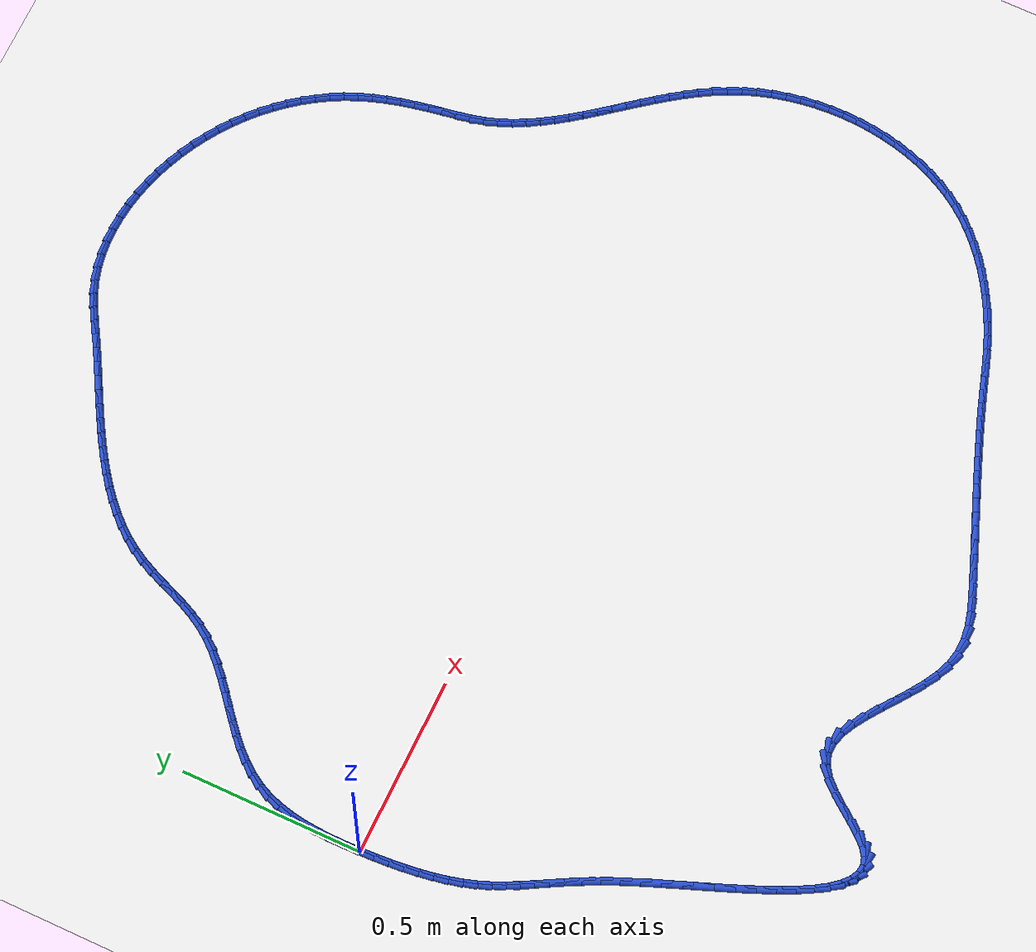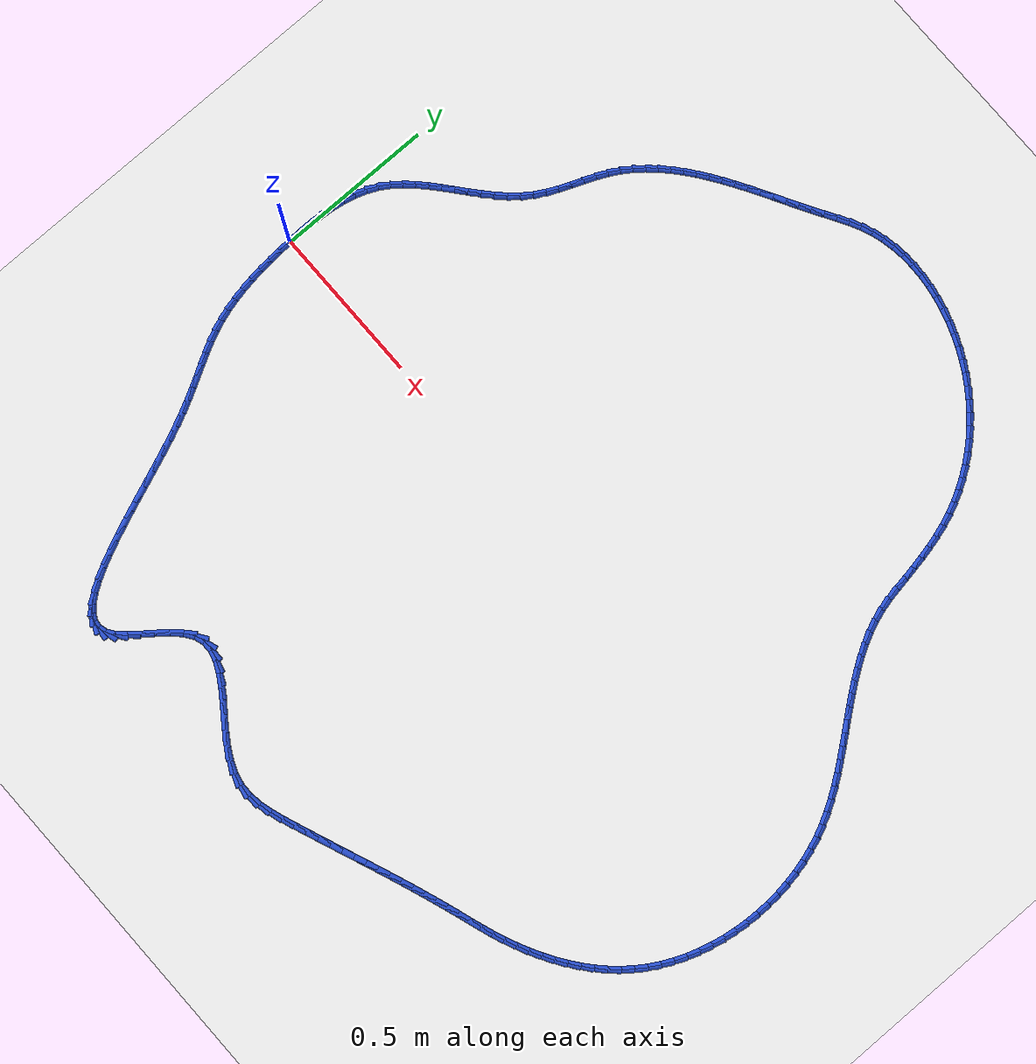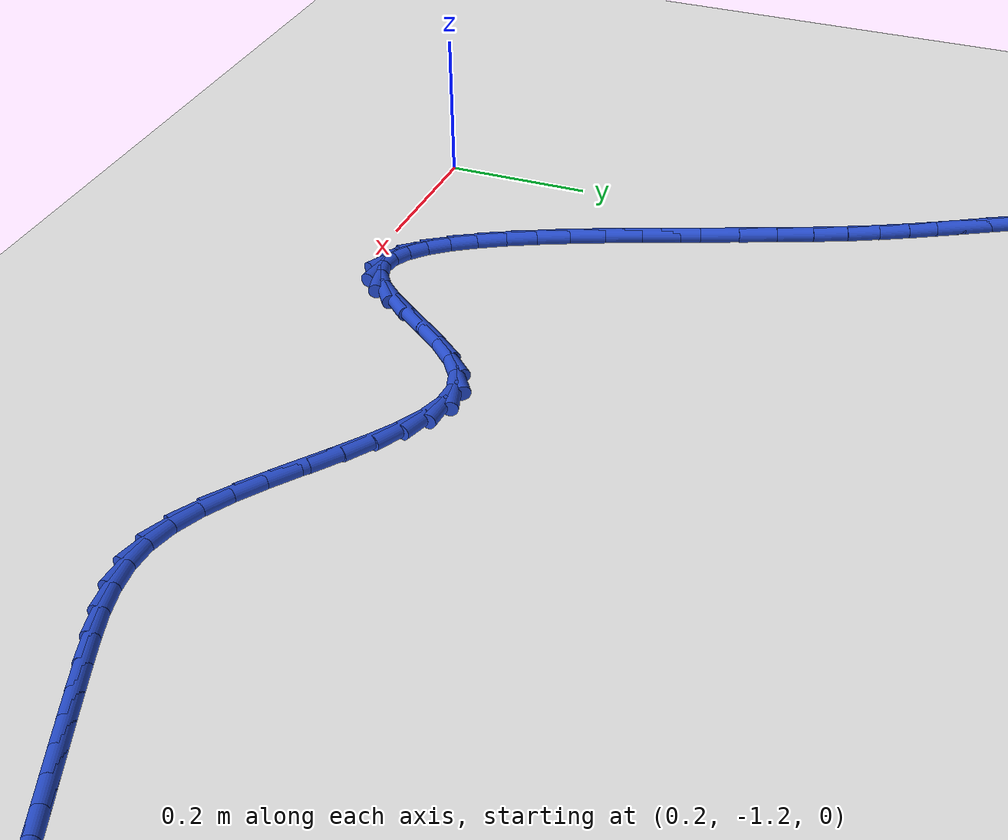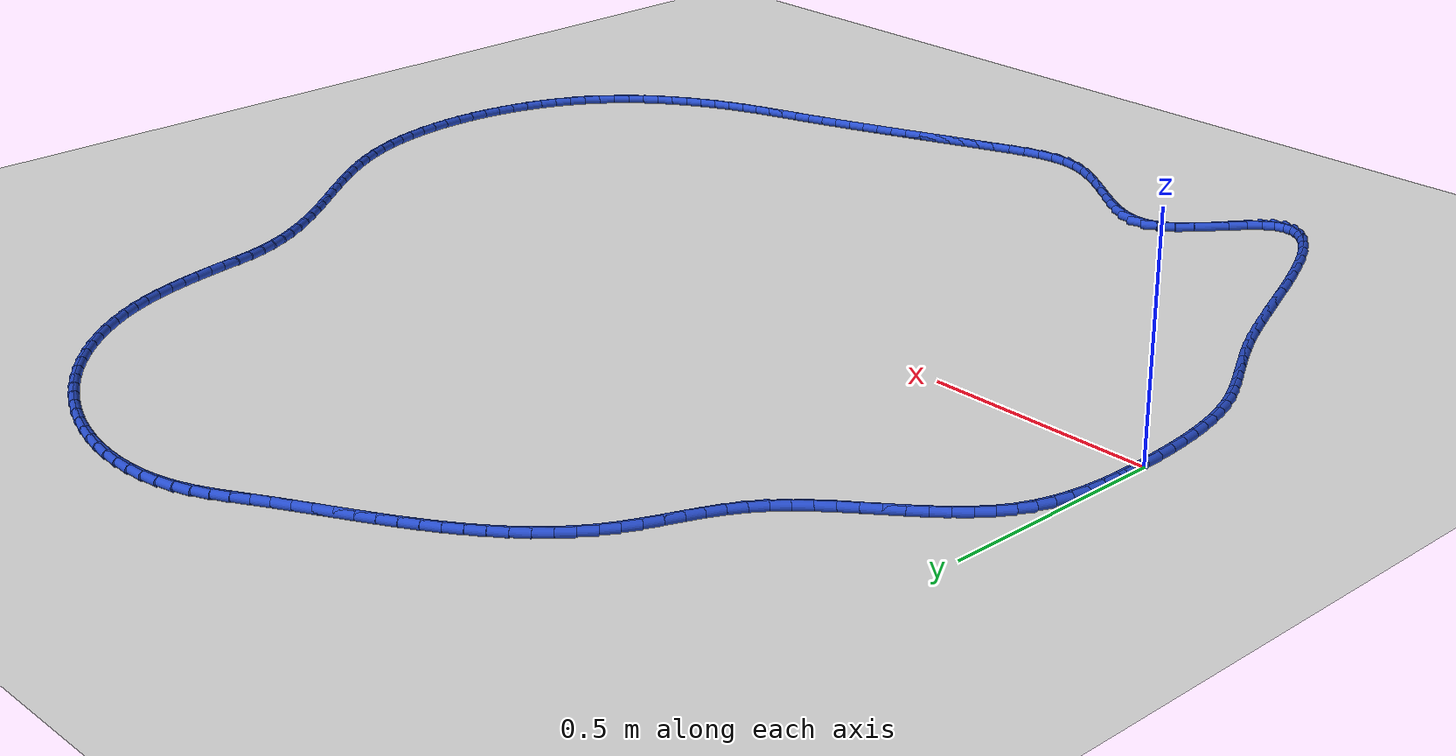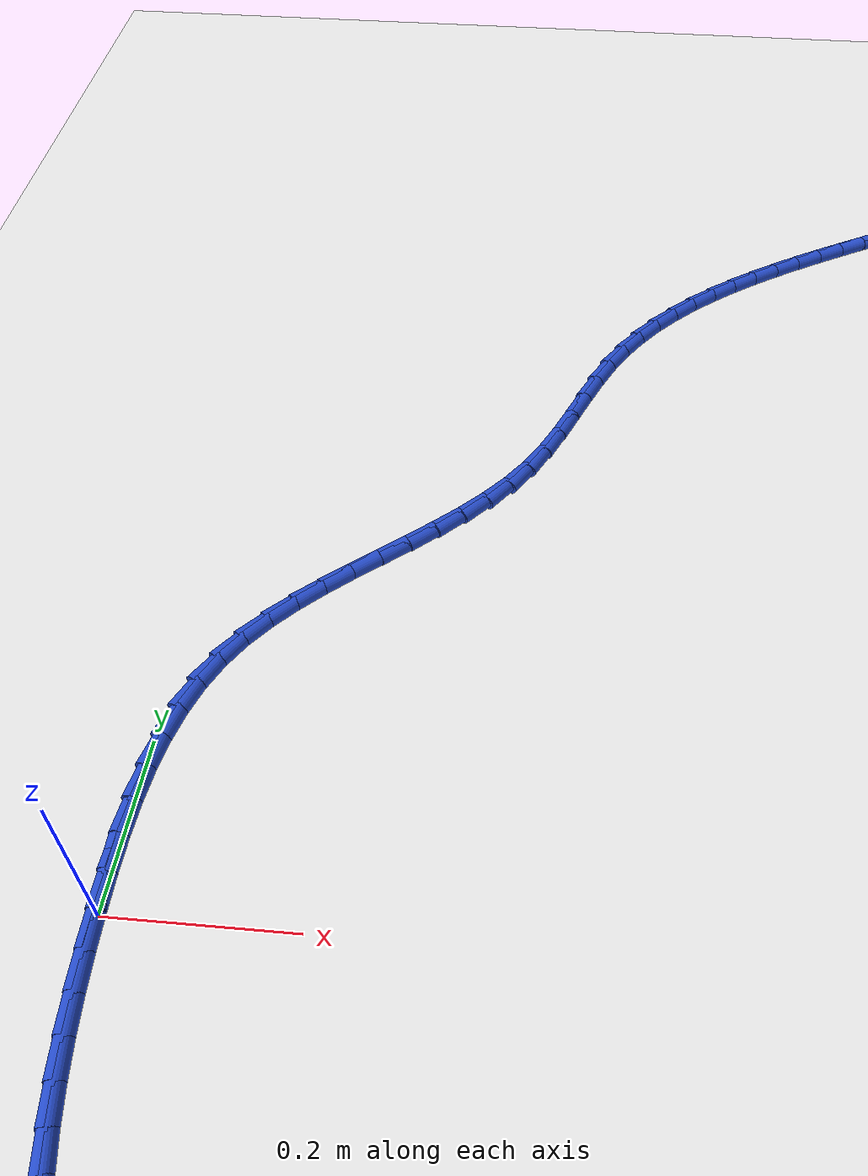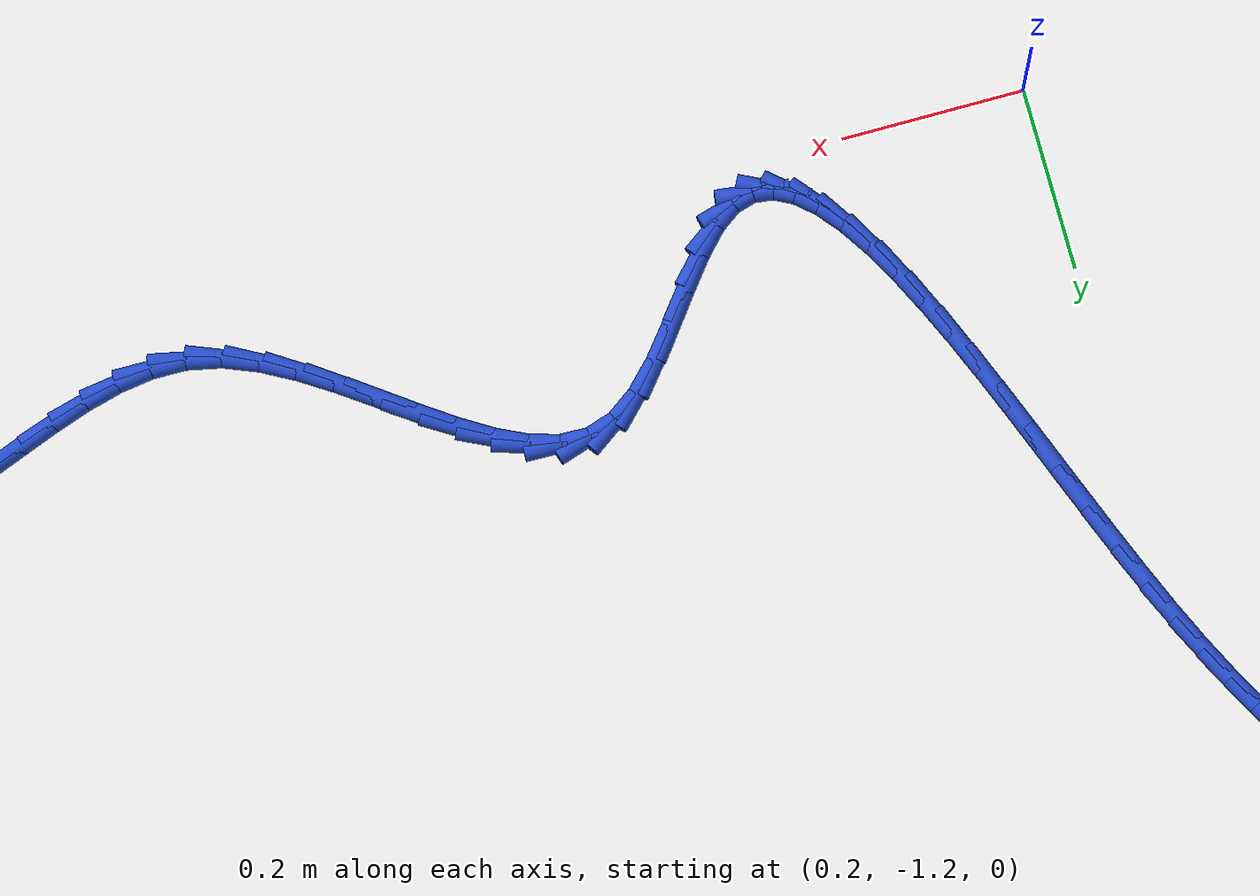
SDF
<sdf version="1.6">
 <world name="default">
  <light name="sun" type="directional">
   <pose>0 0 10 0 -0 0</pose>
   <diffuse>0.8 0.8 0.8 1</diffuse>
   <specular>0.2 0.2 0.2 1</specular>
   <attenuation>
    <range>1000</range>
    <constant>0.9</constant>
    <linear>0.01</linear>
    <quadratic>0.001</quadratic>
   </attenuation>
   <direction>-0.5 0.1 -0.9</direction>
  </light>
  <model name="ground_plane">
   <static>1</static>
   <link name="link">
    <collision name="collision">
     <geometry><plane><normal>0 0 1</normal><size>100 100</size></plane></geometry>
     <surface><friction><ode><mu>100</mu><mu2>50</mu2></ode></friction></surface>
    </collision>
    <visual name="visual">
     <cast_shadows>0</cast_shadows>
     <geometry><plane><normal>0 0 1</normal><size>100 100</size></plane></geometry>
     <material>
      <script><uri>file://media/materials/scripts/gazebo.material</uri><name>Gazebo/WhiteGlow</name></script>
     </material>
    </visual>
   </link>
  </model>
  <gravity>0 0 -9.8</gravity>
  <magnetic_field>6e-06 2.3e-05 -4.2e-05</magnetic_field>
  <atmosphere type="adiabatic"/>
  <physics name="default_physics" default="0" type="ode">
   <max_step_size>0.001</max_step_size>
   <real_time_factor>1</real_time_factor>
   <real_time_update_rate>1000</real_time_update_rate>
  </physics>
  <scene><ambient>0.4 0.4 0.4 1</ambient><background>0.7 0.7 0.7 1</background><shadows>1</shadows></scene>
  <spherical_coordinates>
   <surface_model>EARTH_WGS84</surface_model>
   <latitude_deg>0</latitude_deg>
   <longitude_deg>0</longitude_deg>
   <elevation>0</elevation>
   <heading_deg>0</heading_deg>
  </spherical_coordinates>
  <model name="line">
   <link name="link_0">
    <pose>-3.686287386450715e-17 -3.469446951953614e-17 0.01 0 1.57 -1.5474649795137356</pose>
    <collision name="collision">
     <geometry><cylinder><radius>0.01</radius><length>0.08</length></cylinder></geometry>
    </collision>
    <visual name="visual">
     <material>
      <script><name>Gazebo/Blue</name><uri>file://media/materials/scripts/gazebo.material</uri></script>
     </material>
     <geometry><cylinder><radius>0.01</radius><length>0.08</length></cylinder></geometry>
    </visual>
   </link>
   <link name="link_1">
    <pose>-0.0009463680217165169 0.04055472172470044 0.01 0 1.57 1.5663769954412827</pose>
    <collision name="collision">
     <geometry><cylinder><radius>0.01</radius><length>0.08</length></cylinder></geometry>
    </collision>
    <visual name="visual">
     <material>
      <script><name>Gazebo/Blue</name><uri>file://media/materials/scripts/gazebo.material</uri></script>
     </material>
     <geometry><cylinder><radius>0.01</radius><length>0.08</length></cylinder></geometry>
    </visual>
   </link>
   <link name="link_2">
    <pose>-0.0007676793318576765 0.08098788055961592 0.01 0 1.57 1.5282201143947394</pose>
    <collision name="collision">
     <geometry><cylinder><radius>0.01</radius><length>0.08</length></cylinder></geometry>
    </collision>
    <visual name="visual">
     <material>
      <script><name>Gazebo/Blue</name><uri>file://media/materials/scripts/gazebo.material</uri></script>
     </material>
     <geometry><cylinder><radius>0.01</radius><length>0.08</length></cylinder></geometry>
    </visual>
   </link>
   <link name="link_3">
    <pose>0.0009369492790904928 0.12100079804909797 0.01 0 1.57 1.478640631615229</pose>
    <collision name="collision">
     <geometry><cylinder><radius>0.01</radius><length>0.08</length></cylinder></geometry>
    </collision>
    <visual name="visual">
     <material>
      <script><name>Gazebo/Blue</name><uri>file://media/materials/scripts/gazebo.material</uri></script>
     </material>
     <geometry><cylinder><radius>0.01</radius><length>0.08</length></cylinder></geometry>
    </visual>
   </link>
   <link name="link_4">
    <pose>0.004568401020641995 0.1602947957374982 0.01 0 1.57 1.4163486970955699</pose>
    <collision name="collision">
     <geometry><cylinder><radius>0.01</radius><length>0.08</length></cylinder></geometry>
    </collision>
    <visual name="visual">
     <material>
      <script><name>Gazebo/Blue</name><uri>file://media/materials/scripts/gazebo.material</uri></script>
     </material>
     <geometry><cylinder><radius>0.01</radius><length>0.08</length></cylinder></geometry>
    </visual>
   </link>
   <link name="link_5">
    <pose>0.010527559102310837 0.19857119516916835 0.01 0 1.57 1.3399300408139554</pose>
    <collision name="collision">
     <geometry><cylinder><radius>0.01</radius><length>0.08</length></cylinder></geometry>
    </collision>
    <visual name="visual">
     <material>
      <script><name>Gazebo/Blue</name><uri>file://media/materials/scripts/gazebo.material</uri></script>
     </material>
     <geometry><cylinder><radius>0.01</radius><length>0.08</length></cylinder></geometry>
    </visual>
   </link>
   <link name="link_6">
    <pose>0.019215306733611014 0.23553131788845993 0.01 0 1.57 1.2481421565263737</pose>
    <collision name="collision">
     <geometry><cylinder><radius>0.01</radius><length>0.08</length></cylinder></geometry>
    </collision>
    <visual name="visual">
     <material>
      <script><name>Gazebo/Blue</name><uri>file://media/materials/scripts/gazebo.material</uri></script>
     </material>
     <geometry><cylinder><radius>0.01</radius><length>0.08</length></cylinder></geometry>
    </visual>
   </link>
   <link name="link_7">
    <pose>0.031032527124056554 0.27087648543972465 0.01 0 1.57 1.140421432893402</pose>
    <collision name="collision">
     <geometry><cylinder><radius>0.01</radius><length>0.08</length></cylinder></geometry>
    </collision>
    <visual name="visual">
     <material>
      <script><name>Gazebo/Blue</name><uri>file://media/materials/scripts/gazebo.material</uri></script>
     </material>
     <geometry><cylinder><radius>0.01</radius><length>0.08</length></cylinder></geometry>
    </visual>
   </link>
   <link name="link_8">
    <pose>0.04638010348316142 0.30430801936731405 0.01 0 1.57 1.0210808743892197</pose>
    <collision name="collision">
     <geometry><cylinder><radius>0.01</radius><length>0.08</length></cylinder></geometry>
    </collision>
    <visual name="visual">
     <material>
      <script><name>Gazebo/Blue</name><uri>file://media/materials/scripts/gazebo.material</uri></script>
     </material>
     <geometry><cylinder><radius>0.01</radius><length>0.08</length></cylinder></geometry>
    </visual>
   </link>
   <link name="link_9">
    <pose>0.06555181117323954 0.3355978459254147 0.01 0 1.57 0.9143115836792571</pose>
    <collision name="collision">
     <geometry><cylinder><radius>0.01</radius><length>0.08</length></cylinder></geometry>
    </collision>
    <visual name="visual">
     <material>
      <script><name>Gazebo/Blue</name><uri>file://media/materials/scripts/gazebo.material</uri></script>
     </material>
     <geometry><cylinder><radius>0.01</radius><length>0.08</length></cylinder></geometry>
    </visual>
   </link>
   <link name="link_10">
    <pose>0.08817355723955875 0.36495814528018544 0.01 0 1.57 0.8299035956743306</pose>
    <collision name="collision">
     <geometry><cylinder><radius>0.01</radius><length>0.08</length></cylinder></geometry>
    </collision>
    <visual name="visual">
     <material>
      <script><name>Gazebo/Blue</name><uri>file://media/materials/scripts/gazebo.material</uri></script>
     </material>
     <geometry><cylinder><radius>0.01</radius><length>0.08</length></cylinder></geometry>
    </visual>
   </link>
   <link name="link_11">
    <pose>0.11361428277335917 0.3927704876760648 0.01 0 1.57 0.767310610865753</pose>
    <collision name="collision">
     <geometry><cylinder><radius>0.01</radius><length>0.08</length></cylinder></geometry>
    </collision>
    <visual name="visual">
     <material>
      <script><name>Gazebo/Blue</name><uri>file://media/materials/scripts/gazebo.material</uri></script>
     </material>
     <geometry><cylinder><radius>0.01</radius><length>0.08</length></cylinder></geometry>
    </visual>
   </link>
   <link name="link_12">
    <pose>0.14124239128901275 0.41941679772423235 0.01 0 1.57 0.7251274121420125</pose>
    <collision name="collision">
     <geometry><cylinder><radius>0.01</radius><length>0.08</length></cylinder></geometry>
    </collision>
    <visual name="visual">
     <material>
      <script><name>Gazebo/Blue</name><uri>file://media/materials/scripts/gazebo.material</uri></script>
     </material>
     <geometry><cylinder><radius>0.01</radius><length>0.08</length></cylinder></geometry>
    </visual>
   </link>
   <link name="link_13">
    <pose>0.17042628630089154 0.44527900003586773 0.01 0 1.57 0.7019461398511795</pose>
    <collision name="collision">
     <geometry><cylinder><radius>0.01</radius><length>0.08</length></cylinder></geometry>
    </collision>
    <visual name="visual">
     <material>
      <script><name>Gazebo/Blue</name><uri>file://media/materials/scripts/gazebo.material</uri></script>
     </material>
     <geometry><cylinder><radius>0.01</radius><length>0.08</length></cylinder></geometry>
    </visual>
   </link>
   <link name="link_14">
    <pose>0.2005343713233674 0.4707390192221505 0.01 0 1.57 0.6967898411410958</pose>
    <collision name="collision">
     <geometry><cylinder><radius>0.01</radius><length>0.08</length></cylinder></geometry>
    </collision>
    <visual name="visual">
     <material>
      <script><name>Gazebo/Blue</name><uri>file://media/materials/scripts/gazebo.material</uri></script>
     </material>
     <geometry><cylinder><radius>0.01</radius><length>0.08</length></cylinder></geometry>
    </visual>
   </link>
   <link name="link_15">
    <pose>0.2309350498708123 0.4961787798942602 0.01 0 1.57 0.7092831926135458</pose>
    <collision name="collision">
     <geometry><cylinder><radius>0.01</radius><length>0.08</length></cylinder></geometry>
    </collision>
    <visual name="visual">
     <material>
      <script><name>Gazebo/Blue</name><uri>file://media/materials/scripts/gazebo.material</uri></script>
     </material>
     <geometry><cylinder><radius>0.01</radius><length>0.08</length></cylinder></geometry>
    </visual>
   </link>
   <link name="link_16">
    <pose>0.26099672545759833 0.5219802066633767 0.01 0 1.57 0.7396673547275344</pose>
    <collision name="collision">
     <geometry><cylinder><radius>0.01</radius><length>0.08</length></cylinder></geometry>
    </collision>
    <visual name="visual">
     <material>
      <script><name>Gazebo/Blue</name><uri>file://media/materials/scripts/gazebo.material</uri></script>
     </material>
     <geometry><cylinder><radius>0.01</radius><length>0.08</length></cylinder></geometry>
    </visual>
   </link>
   <link name="link_17">
    <pose>0.29008780159809733 0.5485252241406796 0.01 0 1.57 0.7886913806652952</pose>
    <collision name="collision">
     <geometry><cylinder><radius>0.01</radius><length>0.08</length></cylinder></geometry>
    </collision>
    <visual name="visual">
     <material>
      <script><name>Gazebo/Blue</name><uri>file://media/materials/scripts/gazebo.material</uri></script>
     </material>
     <geometry><cylinder><radius>0.01</radius><length>0.08</length></cylinder></geometry>
    </visual>
   </link>
   <link name="link_18">
    <pose>0.31757668180668125 0.5761957569373483 0.01 0 1.57 0.8573418391484795</pose>
    <collision name="collision">
     <geometry><cylinder><radius>0.01</radius><length>0.08</length></cylinder></geometry>
    </collision>
    <visual name="visual">
     <material>
      <script><name>Gazebo/Blue</name><uri>file://media/materials/scripts/gazebo.material</uri></script>
     </material>
     <geometry><cylinder><radius>0.01</radius><length>0.08</length></cylinder></geometry>
    </visual>
   </link>
   <link name="link_19">
    <pose>0.34283176959772227 0.6053737296645627 0.01 0 1.57 0.9463232186033501</pose>
    <collision name="collision">
     <geometry><cylinder><radius>0.01</radius><length>0.08</length></cylinder></geometry>
    </collision>
    <visual name="visual">
     <material>
      <script><name>Gazebo/Blue</name><uri>file://media/materials/scripts/gazebo.material</uri></script>
     </material>
     <geometry><cylinder><radius>0.01</radius><length>0.08</length></cylinder></geometry>
    </visual>
   </link>
   <link name="link_20">
    <pose>0.36522148282710876 0.6364410575227002 0.01 0 1.57 1.0460938358535734</pose>
    <collision name="collision">
     <geometry><cylinder><radius>0.01</radius><length>0.08</length></cylinder></geometry>
    </collision>
    <visual name="visual">
     <material>
      <script><name>Gazebo/Blue</name><uri>file://media/materials/scripts/gazebo.material</uri></script>
     </material>
     <geometry><cylinder><radius>0.01</radius><length>0.08</length></cylinder></geometry>
    </visual>
   </link>
   <link name="link_21">
    <pose>0.38440731043031406 0.6695873445298335 0.01 0 1.57 1.1228051262349183</pose>
    <collision name="collision">
     <geometry><cylinder><radius>0.01</radius><length>0.08</length></cylinder></geometry>
    </collision>
    <visual name="visual">
     <material>
      <script><name>Gazebo/Blue</name><uri>file://media/materials/scripts/gazebo.material</uri></script>
     </material>
     <geometry><cylinder><radius>0.01</radius><length>0.08</length></cylinder></geometry>
    </visual>
   </link>
   <link name="link_22">
    <pose>0.401097027031503 0.7043156293898974 0.01 0 1.57 1.1694198163277236</pose>
    <collision name="collision">
     <geometry><cylinder><radius>0.01</radius><length>0.08</length></cylinder></geometry>
    </collision>
    <visual name="visual">
     <material>
      <script><name>Gazebo/Blue</name><uri>file://media/materials/scripts/gazebo.material</uri></script>
     </material>
     <geometry><cylinder><radius>0.01</radius><length>0.08</length></cylinder></geometry>
    </visual>
   </link>
   <link name="link_23">
    <pose>0.41623180012360517 0.7399758000469593 0.01 0 1.57 1.1868356369291502</pose>
    <collision name="collision">
     <geometry><cylinder><radius>0.01</radius><length>0.08</length></cylinder></geometry>
    </collision>
    <visual name="visual">
     <material>
      <script><name>Gazebo/Blue</name><uri>file://media/materials/scripts/gazebo.material</uri></script>
     </material>
     <geometry><cylinder><radius>0.01</radius><length>0.08</length></cylinder></geometry>
    </visual>
   </link>
   <link name="link_24">
    <pose>0.4307527971995502 0.775917744445086 0.01 0 1.57 1.1753813466987277</pose>
    <collision name="collision">
     <geometry><cylinder><radius>0.01</radius><length>0.08</length></cylinder></geometry>
    </collision>
    <visual name="visual">
     <material>
      <script><name>Gazebo/Blue</name><uri>file://media/materials/scripts/gazebo.material</uri></script>
     </material>
     <geometry><cylinder><radius>0.01</radius><length>0.08</length></cylinder></geometry>
    </visual>
   </link>
   <link name="link_25">
    <pose>0.4456011857522678 0.8114913505283454 0.01 0 1.57 1.1343781157120894</pose>
    <collision name="collision">
     <geometry><cylinder><radius>0.01</radius><length>0.08</length></cylinder></geometry>
    </collision>
    <visual name="visual">
     <material>
      <script><name>Gazebo/Blue</name><uri>file://media/materials/scripts/gazebo.material</uri></script>
     </material>
     <geometry><cylinder><radius>0.01</radius><length>0.08</length></cylinder></geometry>
    </visual>
   </link>
   <link name="link_26">
    <pose>0.46171813327468786 0.8460465062408045 0.01 0 1.57 1.0635134181555808</pose>
    <collision name="collision">
     <geometry><cylinder><radius>0.01</radius><length>0.08</length></cylinder></geometry>
    </collision>
    <visual name="visual">
     <material>
      <script><name>Gazebo/Blue</name><uri>file://media/materials/scripts/gazebo.material</uri></script>
     </material>
     <geometry><cylinder><radius>0.01</radius><length>0.08</length></cylinder></geometry>
    </visual>
   </link>
   <link name="link_27">
    <pose>0.48000984480563597 0.8789572899281481 0.01 0 1.57 0.9811165591821157</pose>
    <collision name="collision">
     <geometry><cylinder><radius>0.01</radius><length>0.08</length></cylinder></geometry>
    </collision>
    <visual name="visual">
     <material>
      <script><name>Gazebo/Blue</name><uri>file://media/materials/scripts/gazebo.material</uri></script>
     </material>
     <geometry><cylinder><radius>0.01</radius><length>0.08</length></cylinder></geometry>
    </visual>
   </link>
   <link name="link_28">
    <pose>0.5007868933690556 0.9100098956763866 0.01 0 1.57 0.904138031027709</pose>
    <collision name="collision">
     <geometry><cylinder><radius>0.01</radius><length>0.08</length></cylinder></geometry>
    </collision>
    <visual name="visual">
     <material>
      <script><name>Gazebo/Blue</name><uri>file://media/materials/scripts/gazebo.material</uri></script>
     </material>
     <geometry><cylinder><radius>0.01</radius><length>0.08</length></cylinder></geometry>
    </visual>
   </link>
   <link name="link_29">
    <pose>0.5238611774957123 0.9393355487364115 0.01 0 1.57 0.8339819891368229</pose>
    <collision name="collision">
     <geometry><cylinder><radius>0.01</radius><length>0.08</length></cylinder></geometry>
    </collision>
    <visual name="visual">
     <material>
      <script><name>Gazebo/Blue</name><uri>file://media/materials/scripts/gazebo.material</uri></script>
     </material>
     <geometry><cylinder><radius>0.01</radius><length>0.08</length></cylinder></geometry>
    </visual>
   </link>
   <link name="link_30">
    <pose>0.5490292168546135 0.9670761149406167 0.01 0 1.57 0.771136930431407</pose>
    <collision name="collision">
     <geometry><cylinder><radius>0.01</radius><length>0.08</length></cylinder></geometry>
    </collision>
    <visual name="visual">
     <material>
      <script><name>Gazebo/Blue</name><uri>file://media/materials/scripts/gazebo.material</uri></script>
     </material>
     <geometry><cylinder><radius>0.01</radius><length>0.08</length></cylinder></geometry>
    </visual>
   </link>
   <link name="link_31">
    <pose>0.5760875311147672 0.993373460121395 0.01 0 1.57 0.7157484069641468</pose>
    <collision name="collision">
     <geometry><cylinder><radius>0.01</radius><length>0.08</length></cylinder></geometry>
    </collision>
    <visual name="visual">
     <material>
      <script><name>Gazebo/Blue</name><uri>file://media/materials/scripts/gazebo.material</uri></script>
     </material>
     <geometry><cylinder><radius>0.01</radius><length>0.08</length></cylinder></geometry>
    </visual>
   </link>
   <link name="link_32">
    <pose>0.6048326399451809 1.0183694501111396 0.01 0 1.57 0.6677176395451531</pose>
    <collision name="collision">
     <geometry><cylinder><radius>0.01</radius><length>0.08</length></cylinder></geometry>
    </collision>
    <visual name="visual">
     <material>
      <script><name>Gazebo/Blue</name><uri>file://media/materials/scripts/gazebo.material</uri></script>
     </material>
     <geometry><cylinder><radius>0.01</radius><length>0.08</length></cylinder></geometry>
    </visual>
   </link>
   <link name="link_33">
    <pose>0.6350610630148626 1.0422059507422439 0.01 0 1.57 0.6267960547733811</pose>
    <collision name="collision">
     <geometry><cylinder><radius>0.01</radius><length>0.08</length></cylinder></geometry>
    </collision>
    <visual name="visual">
     <material>
      <script><name>Gazebo/Blue</name><uri>file://media/materials/scripts/gazebo.material</uri></script>
     </material>
     <geometry><cylinder><radius>0.01</radius><length>0.08</length></cylinder></geometry>
    </visual>
   </link>
   <link name="link_34">
    <pose>0.6665693199928198 1.0650248278471006 0.01 0 1.57 0.592663236238043</pose>
    <collision name="collision">
     <geometry><cylinder><radius>0.01</radius><length>0.08</length></cylinder></geometry>
    </collision>
    <visual name="visual">
     <material>
      <script><name>Gazebo/Blue</name><uri>file://media/materials/scripts/gazebo.material</uri></script>
     </material>
     <geometry><cylinder><radius>0.01</radius><length>0.08</length></cylinder></geometry>
    </visual>
   </link>
   <link name="link_35">
    <pose>0.6991539305480601 1.0869679472581026 0.01 0 1.57 0.5649850006141625</pose>
    <collision name="collision">
     <geometry><cylinder><radius>0.01</radius><length>0.08</length></cylinder></geometry>
    </collision>
    <visual name="visual">
     <material>
      <script><name>Gazebo/Blue</name><uri>file://media/materials/scripts/gazebo.material</uri></script>
     </material>
     <geometry><cylinder><radius>0.01</radius><length>0.08</length></cylinder></geometry>
    </visual>
   </link>
   <link name="link_36">
    <pose>0.7326114143495912 1.1081771748076439 0.01 0 1.57 0.5434535553250549</pose>
    <collision name="collision">
     <geometry><cylinder><radius>0.01</radius><length>0.08</length></cylinder></geometry>
    </collision>
    <visual name="visual">
     <material>
      <script><name>Gazebo/Blue</name><uri>file://media/materials/scripts/gazebo.material</uri></script>
     </material>
     <geometry><cylinder><radius>0.01</radius><length>0.08</length></cylinder></geometry>
    </visual>
   </link>
   <link name="link_37">
    <pose>0.7667382910664209 1.128794376328117 0.01 0 1.57 0.5278137370952024</pose>
    <collision name="collision">
     <geometry><cylinder><radius>0.01</radius><length>0.08</length></cylinder></geometry>
    </collision>
    <visual name="visual">
     <material>
      <script><name>Gazebo/Blue</name><uri>file://media/materials/scripts/gazebo.material</uri></script>
     </material>
     <geometry><cylinder><radius>0.01</radius><length>0.08</length></cylinder></geometry>
    </visual>
   </link>
   <link name="link_38">
    <pose>0.8013310803675571 1.1489614176519152 0.01 0 1.57 0.5178794785000909</pose>
    <collision name="collision">
     <geometry><cylinder><radius>0.01</radius><length>0.08</length></cylinder></geometry>
    </collision>
    <visual name="visual">
     <material>
      <script><name>Gazebo/Blue</name><uri>file://media/materials/scripts/gazebo.material</uri></script>
     </material>
     <geometry><cylinder><radius>0.01</radius><length>0.08</length></cylinder></geometry>
    </visual>
   </link>
   <link name="link_39">
    <pose>0.8361863019220074 1.1688201646114313 0.01 0 1.57 0.5135439406419681</pose>
    <collision name="collision">
     <geometry><cylinder><radius>0.01</radius><length>0.08</length></cylinder></geometry>
    </collision>
    <visual name="visual">
     <material>
      <script><name>Gazebo/Blue</name><uri>file://media/materials/scripts/gazebo.material</uri></script>
     </material>
     <geometry><cylinder><radius>0.01</radius><length>0.08</length></cylinder></geometry>
    </visual>
   </link>
   <link name="link_40">
    <pose>0.8711004753987794 1.1885124830390592 0.01 0 1.57 0.5147857849634769</pose>
    <collision name="collision">
     <geometry><cylinder><radius>0.01</radius><length>0.08</length></cylinder></geometry>
    </collision>
    <visual name="visual">
     <material>
      <script><name>Gazebo/Blue</name><uri>file://media/materials/scripts/gazebo.material</uri></script>
     </material>
     <geometry><cylinder><radius>0.01</radius><length>0.08</length></cylinder></geometry>
    </visual>
   </link>
   <link name="link_41">
    <pose>0.9058701204668809 1.2081802387671914 0.01 0 1.57 0.5216730932892976</pose>
    <collision name="collision">
     <geometry><cylinder><radius>0.01</radius><length>0.08</length></cylinder></geometry>
    </collision>
    <visual name="visual">
     <material>
      <script><name>Gazebo/Blue</name><uri>file://media/materials/scripts/gazebo.material</uri></script>
     </material>
     <geometry><cylinder><radius>0.01</radius><length>0.08</length></cylinder></geometry>
    </visual>
   </link>
   <link name="link_42">
    <pose>0.9402917567953191 1.227965297628221 0.01 0 1.57 0.5343183449423123</pose>
    <collision name="collision">
     <geometry><cylinder><radius>0.01</radius><length>0.08</length></cylinder></geometry>
    </collision>
    <visual name="visual">
     <material>
      <script><name>Gazebo/Blue</name><uri>file://media/materials/scripts/gazebo.material</uri></script>
     </material>
     <geometry><cylinder><radius>0.01</radius><length>0.08</length></cylinder></geometry>
    </visual>
   </link>
   <link name="link_43">
    <pose>0.9741629299014147 1.2480079746376391 0.01 0 1.57 0.5426977365664463</pose>
    <collision name="collision">
     <geometry><cylinder><radius>0.01</radius><length>0.08</length></cylinder></geometry>
    </collision>
    <visual name="visual">
     <material>
      <script><name>Gazebo/Blue</name><uri>file://media/materials/scripts/gazebo.material</uri></script>
     </material>
     <geometry><cylinder><radius>0.01</radius><length>0.08</length></cylinder></geometry>
    </visual>
   </link>
   <link name="link_44">
    <pose>1.00750195938174 1.2681148315946167 0.01 0 1.57 0.5234529172749014</pose>
    <collision name="collision">
     <geometry><cylinder><radius>0.01</radius><length>0.08</length></cylinder></geometry>
    </collision>
    <visual name="visual">
     <material>
      <script><name>Gazebo/Blue</name><uri>file://media/materials/scripts/gazebo.material</uri></script>
     </material>
     <geometry><cylinder><radius>0.01</radius><length>0.08</length></cylinder></geometry>
    </visual>
   </link>
   <link name="link_45">
    <pose>1.040821368642361 1.287345322161835 0.01 0 1.57 0.4724021816477018</pose>
    <collision name="collision">
     <geometry><cylinder><radius>0.01</radius><length>0.08</length></cylinder></geometry>
    </collision>
    <visual name="visual">
     <material>
      <script><name>Gazebo/Blue</name><uri>file://media/materials/scripts/gazebo.material</uri></script>
     </material>
     <geometry><cylinder><radius>0.01</radius><length>0.08</length></cylinder></geometry>
    </visual>
   </link>
   <link name="link_46">
    <pose>1.0747008030936385 1.3046574289194286 0.01 0 1.57 0.3898643542541057</pose>
    <collision name="collision">
     <geometry><cylinder><radius>0.01</radius><length>0.08</length></cylinder></geometry>
    </collision>
    <visual name="visual">
     <material>
      <script><name>Gazebo/Blue</name><uri>file://media/materials/scripts/gazebo.material</uri></script>
     </material>
     <geometry><cylinder><radius>0.01</radius><length>0.08</length></cylinder></geometry>
    </visual>
   </link>
   <link name="link_47">
    <pose>1.1097000070043581 1.3190384743640073 0.01 0 1.57 0.2948778086860935</pose>
    <collision name="collision">
     <geometry><cylinder><radius>0.01</radius><length>0.08</length></cylinder></geometry>
    </collision>
    <visual name="visual">
     <material>
      <script><name>Gazebo/Blue</name><uri>file://media/materials/scripts/gazebo.material</uri></script>
     </material>
     <geometry><cylinder><radius>0.01</radius><length>0.08</length></cylinder></geometry>
    </visual>
   </link>
   <link name="link_48">
    <pose>1.1459832156904328 1.3300588731528682 0.01 0 1.57 0.20492092542615195</pose>
    <collision name="collision">
     <geometry><cylinder><radius>0.01</radius><length>0.08</length></cylinder></geometry>
    </collision>
    <visual name="visual">
     <material>
      <script><name>Gazebo/Blue</name><uri>file://media/materials/scripts/gazebo.material</uri></script>
     </material>
     <geometry><cylinder><radius>0.01</radius><length>0.08</length></cylinder></geometry>
    </visual>
   </link>
   <link name="link_49">
    <pose>1.1833509128777688 1.3378253127609787 0.01 0 1.57 0.12072873864360992</pose>
    <collision name="collision">
     <geometry><cylinder><radius>0.01</radius><length>0.08</length></cylinder></geometry>
    </collision>
    <visual name="visual">
     <material>
      <script><name>Gazebo/Blue</name><uri>file://media/materials/scripts/gazebo.material</uri></script>
     </material>
     <geometry><cylinder><radius>0.01</radius><length>0.08</length></cylinder></geometry>
    </visual>
   </link>
   <link name="link_50">
    <pose>1.2215900465760243 1.3424644361408657 0.01 0 1.57 0.042097341559704966</pose>
    <collision name="collision">
     <geometry><cylinder><radius>0.01</radius><length>0.08</length></cylinder></geometry>
    </collision>
    <visual name="visual">
     <material>
      <script><name>Gazebo/Blue</name><uri>file://media/materials/scripts/gazebo.material</uri></script>
     </material>
     <geometry><cylinder><radius>0.01</radius><length>0.08</length></cylinder></geometry>
    </visual>
   </link>
   <link name="link_51">
    <pose>1.2604875647948566 1.3441028862450553 0.01 0 1.57 -0.031395138302547976</pose>
    <collision name="collision">
     <geometry><cylinder><radius>0.01</radius><length>0.08</length></cylinder></geometry>
    </collision>
    <visual name="visual">
     <material>
      <script><name>Gazebo/Blue</name><uri>file://media/materials/scripts/gazebo.material</uri></script>
     </material>
     <geometry><cylinder><radius>0.01</radius><length>0.08</length></cylinder></geometry>
    </visual>
   </link>
   <link name="link_52">
    <pose>1.2998304155439244 1.3428673060260736 0.01 0 1.57 -0.10030543693854967</pose>
    <collision name="collision">
     <geometry><cylinder><radius>0.01</radius><length>0.08</length></cylinder></geometry>
    </collision>
    <visual name="visual">
     <material>
      <script><name>Gazebo/Blue</name><uri>file://media/materials/scripts/gazebo.material</uri></script>
     </material>
     <geometry><cylinder><radius>0.01</radius><length>0.08</length></cylinder></geometry>
    </visual>
   </link>
   <link name="link_53">
    <pose>1.3394055468328856 1.3388843384364473 0.01 0 1.57 -0.16526299212392126</pose>
    <collision name="collision">
     <geometry><cylinder><radius>0.01</radius><length>0.08</length></cylinder></geometry>
    </collision>
    <visual name="visual">
     <material>
      <script><name>Gazebo/Blue</name><uri>file://media/materials/scripts/gazebo.material</uri></script>
     </material>
     <geometry><cylinder><radius>0.01</radius><length>0.08</length></cylinder></geometry>
    </visual>
   </link>
   <link name="link_54">
    <pose>1.3789999066713992 1.3322806264287037 0.01 0 1.57 -0.22692853462692986</pose>
    <collision name="collision">
     <geometry><cylinder><radius>0.01</radius><length>0.08</length></cylinder></geometry>
    </collision>
    <visual name="visual">
     <material>
      <script><name>Gazebo/Blue</name><uri>file://media/materials/scripts/gazebo.material</uri></script>
     </material>
     <geometry><cylinder><radius>0.01</radius><length>0.08</length></cylinder></geometry>
    </visual>
   </link>
   <link name="link_55">
    <pose>1.4184004430691222 1.3231828129553687 0.01 0 1.57 -0.2859699649763472</pose>
    <collision name="collision">
     <geometry><cylinder><radius>0.01</radius><length>0.08</length></cylinder></geometry>
    </collision>
    <visual name="visual">
     <material>
      <script><name>Gazebo/Blue</name><uri>file://media/materials/scripts/gazebo.material</uri></script>
     </material>
     <geometry><cylinder><radius>0.01</radius><length>0.08</length></cylinder></geometry>
    </visual>
   </link>
   <link name="link_56">
    <pose>1.457394104035713 1.3117175409689683 0.01 0 1.57 -0.34305127444333555</pose>
    <collision name="collision">
     <geometry><cylinder><radius>0.01</radius><length>0.08</length></cylinder></geometry>
    </collision>
    <visual name="visual">
     <material>
      <script><name>Gazebo/Blue</name><uri>file://media/materials/scripts/gazebo.material</uri></script>
     </material>
     <geometry><cylinder><radius>0.01</radius><length>0.08</length></cylinder></geometry>
    </visual>
   </link>
   <link name="link_57">
    <pose>1.4957678375808297 1.2980114534220297 0.01 0 1.57 -0.39883073174027717</pose>
    <collision name="collision">
     <geometry><cylinder><radius>0.01</radius><length>0.08</length></cylinder></geometry>
    </collision>
    <visual name="visual">
     <material>
      <script><name>Gazebo/Blue</name><uri>file://media/materials/scripts/gazebo.material</uri></script>
     </material>
     <geometry><cylinder><radius>0.01</radius><length>0.08</length></cylinder></geometry>
    </visual>
   </link>
   <link name="link_58">
    <pose>1.5333085917141303 1.2821911932670793 0.01 0 1.57 -0.45396535825029377</pose>
    <collision name="collision">
     <geometry><cylinder><radius>0.01</radius><length>0.08</length></cylinder></geometry>
    </collision>
    <visual name="visual">
     <material>
      <script><name>Gazebo/Blue</name><uri>file://media/materials/scripts/gazebo.material</uri></script>
     </material>
     <geometry><cylinder><radius>0.01</radius><length>0.08</length></cylinder></geometry>
    </visual>
   </link>
   <link name="link_59">
    <pose>1.5698033365688513 1.2643833956277164 0.01 0 1.57 -0.5089949627493194</pose>
    <collision name="collision">
     <geometry><cylinder><radius>0.01</radius><length>0.08</length></cylinder></geometry>
    </collision>
    <visual name="visual">
     <material>
      <script><name>Gazebo/Blue</name><uri>file://media/materials/scripts/gazebo.material</uri></script>
     </material>
     <geometry><cylinder><radius>0.01</radius><length>0.08</length></cylinder></geometry>
    </visual>
   </link>
   <link name="link_60">
    <pose>1.6050672943729332 1.2447046979870533 0.01 0 1.57 -0.5639861529377335</pose>
    <collision name="collision">
     <geometry><cylinder><radius>0.01</radius><length>0.08</length></cylinder></geometry>
    </collision>
    <visual name="visual">
     <material>
      <script><name>Gazebo/Blue</name><uri>file://media/materials/scripts/gazebo.material</uri></script>
     </material>
     <geometry><cylinder><radius>0.01</radius><length>0.08</length></cylinder></geometry>
    </visual>
   </link>
   <link name="link_61">
    <pose>1.6389992879424893 1.223242153875795 0.01 0 1.57 -0.6190331217928586</pose>
    <collision name="collision">
     <geometry><cylinder><radius>0.01</radius><length>0.08</length></cylinder></geometry>
    </collision>
    <visual name="visual">
     <material>
      <script><name>Gazebo/Blue</name><uri>file://media/materials/scripts/gazebo.material</uri></script>
     </material>
     <geometry><cylinder><radius>0.01</radius><length>0.08</length></cylinder></geometry>
    </visual>
   </link>
   <link name="link_62">
    <pose>1.6715135299659178 1.2000773707714638 0.01 0 1.57 -0.6742856245499746</pose>
    <collision name="collision">
     <geometry><cylinder><radius>0.01</radius><length>0.08</length></cylinder></geometry>
    </collision>
    <visual name="visual">
     <material>
      <script><name>Gazebo/Blue</name><uri>file://media/materials/scripts/gazebo.material</uri></script>
     </material>
     <geometry><cylinder><radius>0.01</radius><length>0.08</length></cylinder></geometry>
    </visual>
   </link>
   <link name="link_63">
    <pose>1.702524233131617 1.1752919561515842 0.01 0 1.57 -0.729900577716644</pose>
    <collision name="collision">
     <geometry><cylinder><radius>0.01</radius><length>0.08</length></cylinder></geometry>
    </collision>
    <visual name="visual">
     <material>
      <script><name>Gazebo/Blue</name><uri>file://media/materials/scripts/gazebo.material</uri></script>
     </material>
     <geometry><cylinder><radius>0.01</radius><length>0.08</length></cylinder></geometry>
    </visual>
   </link>
   <link name="link_64">
    <pose>1.7319456101279849 1.148967517493678 0.01 0 1.57 -0.7860391305130573</pose>
    <collision name="collision">
     <geometry><cylinder><radius>0.01</radius><length>0.08</length></cylinder></geometry>
    </collision>
    <visual name="visual">
     <material>
      <script><name>Gazebo/Blue</name><uri>file://media/materials/scripts/gazebo.material</uri></script>
     </material>
     <geometry><cylinder><radius>0.01</radius><length>0.08</length></cylinder></geometry>
    </visual>
   </link>
   <link name="link_65">
    <pose>1.7596918736434195 1.1211856622752692 0.01 0 1.57 -0.8428634325704437</pose>
    <collision name="collision">
     <geometry><cylinder><radius>0.01</radius><length>0.08</length></cylinder></geometry>
    </collision>
    <visual name="visual">
     <material>
      <script><name>Gazebo/Blue</name><uri>file://media/materials/scripts/gazebo.material</uri></script>
     </material>
     <geometry><cylinder><radius>0.01</radius><length>0.08</length></cylinder></geometry>
    </visual>
   </link>
   <link name="link_66">
    <pose>1.7856772363663191 1.0920279979738807 0.01 0 1.57 -0.9005329580310644</pose>
    <collision name="collision">
     <geometry><cylinder><radius>0.01</radius><length>0.08</length></cylinder></geometry>
    </collision>
    <visual name="visual">
     <material>
      <script><name>Gazebo/Blue</name><uri>file://media/materials/scripts/gazebo.material</uri></script>
     </material>
     <geometry><cylinder><radius>0.01</radius><length>0.08</length></cylinder></geometry>
    </visual>
   </link>
   <link name="link_67">
    <pose>1.8098159109850809 1.0615761320670354 0.01 0 1.57 -0.9592002456315628</pose>
    <collision name="collision">
     <geometry><cylinder><radius>0.01</radius><length>0.08</length></cylinder></geometry>
    </collision>
    <visual name="visual">
     <material>
      <script><name>Gazebo/Blue</name><uri>file://media/materials/scripts/gazebo.material</uri></script>
     </material>
     <geometry><cylinder><radius>0.01</radius><length>0.08</length></cylinder></geometry>
    </visual>
   </link>
   <link name="link_68">
    <pose>1.8320221101881038 1.0299116720322565 0.01 0 1.57 -1.0190059330663983</pose>
    <collision name="collision">
     <geometry><cylinder><radius>0.01</radius><length>0.08</length></cylinder></geometry>
    </collision>
    <visual name="visual">
     <material>
      <script><name>Gazebo/Blue</name><uri>file://media/materials/scripts/gazebo.material</uri></script>
     </material>
     <geometry><cylinder><radius>0.01</radius><length>0.08</length></cylinder></geometry>
    </visual>
   </link>
   <link name="link_69">
    <pose>1.852210046663786 0.9971162253470678 0.01 0 1.57 -1.080073008997513</pose>
    <collision name="collision">
     <geometry><cylinder><radius>0.01</radius><length>0.08</length></cylinder></geometry>
    </collision>
    <visual name="visual">
     <material>
      <script><name>Gazebo/Blue</name><uri>file://media/materials/scripts/gazebo.material</uri></script>
     </material>
     <geometry><cylinder><radius>0.01</radius><length>0.08</length></cylinder></geometry>
    </visual>
   </link>
   <link name="link_70">
    <pose>1.8702939331005255 0.9632713994889917 0.01 0 1.57 -1.1425002853315396</pose>
    <collision name="collision">
     <geometry><cylinder><radius>0.01</radius><length>0.08</length></cylinder></geometry>
    </collision>
    <visual name="visual">
     <material>
      <script><name>Gazebo/Blue</name><uri>file://media/materials/scripts/gazebo.material</uri></script>
     </material>
     <geometry><cylinder><radius>0.01</radius><length>0.08</length></cylinder></geometry>
    </visual>
   </link>
   <link name="link_71">
    <pose>1.886187982186719 0.9284588019355517 0.01 0 1.57 -1.2054431026894072</pose>
    <collision name="collision">
     <geometry><cylinder><radius>0.01</radius><length>0.08</length></cylinder></geometry>
    </collision>
    <visual name="visual">
     <material>
      <script><name>Gazebo/Blue</name><uri>file://media/materials/scripts/gazebo.material</uri></script>
     </material>
     <geometry><cylinder><radius>0.01</radius><length>0.08</length></cylinder></geometry>
    </visual>
   </link>
   <link name="link_72">
    <pose>1.899841794475258 0.892765072195211 0.01 0 1.57 -1.2618885638139103</pose>
    <collision name="collision">
     <geometry><cylinder><radius>0.01</radius><length>0.08</length></cylinder></geometry>
    </collision>
    <visual name="visual">
     <material>
      <script><name>Gazebo/Blue</name><uri>file://media/materials/scripts/gazebo.material</uri></script>
     </material>
     <geometry><cylinder><radius>0.01</radius><length>0.08</length></cylinder></geometry>
    </visual>
   </link>
   <link name="link_73">
    <pose>1.9114738467684727 0.8563150830415853 0.01 0 1.57 -1.3084685962550366</pose>
    <collision name="collision">
     <geometry><cylinder><radius>0.01</radius><length>0.08</length></cylinder></geometry>
    </collision>
    <visual name="visual">
     <material>
      <script><name>Gazebo/Blue</name><uri>file://media/materials/scripts/gazebo.material</uri></script>
     </material>
     <geometry><cylinder><radius>0.01</radius><length>0.08</length></cylinder></geometry>
    </visual>
   </link>
   <link name="link_74">
    <pose>1.9214260594178705 0.8192512604905597 0.01 0 1.57 -1.3451869962194523</pose>
    <collision name="collision">
     <geometry><cylinder><radius>0.01</radius><length>0.08</length></cylinder></geometry>
    </collision>
    <visual name="visual">
     <material>
      <script><name>Gazebo/Blue</name><uri>file://media/materials/scripts/gazebo.material</uri></script>
     </material>
     <geometry><cylinder><radius>0.01</radius><length>0.08</length></cylinder></geometry>
    </visual>
   </link>
   <link name="link_75">
    <pose>1.9300410007329047 0.7817161226953807 0.01 0 1.57 -1.3721960520323866</pose>
    <collision name="collision">
     <geometry><cylinder><radius>0.01</radius><length>0.08</length></cylinder></geometry>
    </collision>
    <visual name="visual">
     <material>
      <script><name>Gazebo/Blue</name><uri>file://media/materials/scripts/gazebo.material</uri></script>
     </material>
     <geometry><cylinder><radius>0.01</radius><length>0.08</length></cylinder></geometry>
    </visual>
   </link>
   <link name="link_76">
    <pose>1.9376612390230274 0.7438521878092934 0.01 0 1.57 -1.3896740966101542</pose>
    <collision name="collision">
     <geometry><cylinder><radius>0.01</radius><length>0.08</length></cylinder></geometry>
    </collision>
    <visual name="visual">
     <material>
      <script><name>Gazebo/Blue</name><uri>file://media/materials/scripts/gazebo.material</uri></script>
     </material>
     <geometry><cylinder><radius>0.01</radius><length>0.08</length></cylinder></geometry>
    </visual>
   </link>
   <link name="link_77">
    <pose>1.9446293425976904 0.7058019739855439 0.01 0 1.57 -1.3976938696370937</pose>
    <collision name="collision">
     <geometry><cylinder><radius>0.01</radius><length>0.08</length></cylinder></geometry>
    </collision>
    <visual name="visual">
     <material>
      <script><name>Gazebo/Blue</name><uri>file://media/materials/scripts/gazebo.material</uri></script>
     </material>
     <geometry><cylinder><radius>0.01</radius><length>0.08</length></cylinder></geometry>
    </visual>
   </link>
   <link name="link_78">
    <pose>1.9512900071246404 0.6677089069264774 0.01 0 1.57 -1.3842742013031442</pose>
    <collision name="collision">
     <geometry><cylinder><radius>0.01</radius><length>0.08</length></cylinder></geometry>
    </collision>
    <visual name="visual">
     <material>
      <script><name>Gazebo/Blue</name><uri>file://media/materials/scripts/gazebo.material</uri></script>
     </material>
     <geometry><cylinder><radius>0.01</radius><length>0.08</length></cylinder></geometry>
    </visual>
   </link>
   <link name="link_79">
    <pose>1.9584246303310406 0.6299027131385778 0.01 0 1.57 -1.323874358294375</pose>
    <collision name="collision">
     <geometry><cylinder><radius>0.01</radius><length>0.08</length></cylinder></geometry>
    </collision>
    <visual name="visual">
     <material>
      <script><name>Gazebo/Blue</name><uri>file://media/materials/scripts/gazebo.material</uri></script>
     </material>
     <geometry><cylinder><radius>0.01</radius><length>0.08</length></cylinder></geometry>
    </visual>
   </link>
   <link name="link_80">
    <pose>1.967703436772215 0.5930916597823828 0.01 0 1.57 -1.243899537816027</pose>
    <collision name="collision">
     <geometry><cylinder><radius>0.01</radius><length>0.08</length></cylinder></geometry>
    </collision>
    <visual name="visual">
     <material>
      <script><name>Gazebo/Blue</name><uri>file://media/materials/scripts/gazebo.material</uri></script>
     </material>
     <geometry><cylinder><radius>0.01</radius><length>0.08</length></cylinder></geometry>
    </visual>
   </link>
   <link name="link_81">
    <pose>1.979760217867356 0.5575323584339723 0.01 0 1.57 -1.1704270202718776</pose>
    <collision name="collision">
     <geometry><cylinder><radius>0.01</radius><length>0.08</length></cylinder></geometry>
    </collision>
    <visual name="visual">
     <material>
      <script><name>Gazebo/Blue</name><uri>file://media/materials/scripts/gazebo.material</uri></script>
     </material>
     <geometry><cylinder><radius>0.01</radius><length>0.08</length></cylinder></geometry>
    </visual>
   </link>
   <link name="link_82">
    <pose>1.9943358474853345 0.5230932176683418 0.01 0 1.57 -1.1051795002723537</pose>
    <collision name="collision">
     <geometry><cylinder><radius>0.01</radius><length>0.08</length></cylinder></geometry>
    </collision>
    <visual name="visual">
     <material>
      <script><name>Gazebo/Blue</name><uri>file://media/materials/scripts/gazebo.material</uri></script>
     </material>
     <geometry><cylinder><radius>0.01</radius><length>0.08</length></cylinder></geometry>
    </visual>
   </link>
   <link name="link_83">
    <pose>2.011148510317701 0.48963278176033315 0.01 0 1.57 -1.0487421136812345</pose>
    <collision name="collision">
     <geometry><cylinder><radius>0.01</radius><length>0.08</length></cylinder></geometry>
    </collision>
    <visual name="visual">
     <material>
      <script><name>Gazebo/Blue</name><uri>file://media/materials/scripts/gazebo.material</uri></script>
     </material>
     <geometry><cylinder><radius>0.01</radius><length>0.08</length></cylinder></geometry>
    </visual>
   </link>
   <link name="link_84">
    <pose>2.0299163910560027 0.4570095949847887 0.01 0 1.57 -1.0013109159219804</pose>
    <collision name="collision">
     <geometry><cylinder><radius>0.01</radius><length>0.08</length></cylinder></geometry>
    </collision>
    <visual name="visual">
     <material>
      <script><name>Gazebo/Blue</name><uri>file://media/materials/scripts/gazebo.material</uri></script>
     </material>
     <geometry><cylinder><radius>0.01</radius><length>0.08</length></cylinder></geometry>
    </visual>
   </link>
   <link name="link_85">
    <pose>2.05035767439179 0.42508220161654936 0.01 0 1.57 -0.9628195876552326</pose>
    <collision name="collision">
     <geometry><cylinder><radius>0.01</radius><length>0.08</length></cylinder></geometry>
    </collision>
    <visual name="visual">
     <material>
      <script><name>Gazebo/Blue</name><uri>file://media/materials/scripts/gazebo.material</uri></script>
     </material>
     <geometry><cylinder><radius>0.01</radius><length>0.08</length></cylinder></geometry>
    </visual>
   </link>
   <link name="link_86">
    <pose>2.0721905450166114 0.39370914593045736 0.01 0 1.57 -0.933056085915932</pose>
    <collision name="collision">
     <geometry><cylinder><radius>0.01</radius><length>0.08</length></cylinder></geometry>
    </collision>
    <visual name="visual">
     <material>
      <script><name>Gazebo/Blue</name><uri>file://media/materials/scripts/gazebo.material</uri></script>
     </material>
     <geometry><cylinder><radius>0.01</radius><length>0.08</length></cylinder></geometry>
    </visual>
   </link>
   <link name="link_87">
    <pose>2.095133187622016 0.3627489722013545 0.01 0 1.57 -0.9117546309803627</pose>
    <collision name="collision">
     <geometry><cylinder><radius>0.01</radius><length>0.08</length></cylinder></geometry>
    </collision>
    <visual name="visual">
     <material>
      <script><name>Gazebo/Blue</name><uri>file://media/materials/scripts/gazebo.material</uri></script>
     </material>
     <geometry><cylinder><radius>0.01</radius><length>0.08</length></cylinder></geometry>
    </visual>
   </link>
   <link name="link_88">
    <pose>2.1189037868995526 0.3320602247040827 0.01 0 1.57 -0.8986603636766799</pose>
    <collision name="collision">
     <geometry><cylinder><radius>0.01</radius><length>0.08</length></cylinder></geometry>
    </collision>
    <visual name="visual">
     <material>
      <script><name>Gazebo/Blue</name><uri>file://media/materials/scripts/gazebo.material</uri></script>
     </material>
     <geometry><cylinder><radius>0.01</radius><length>0.08</length></cylinder></geometry>
    </visual>
   </link>
   <link name="link_89">
    <pose>2.1432205275407705 0.30150144771348364 0.01 0 1.57 -0.8935699384710587</pose>
    <collision name="collision">
     <geometry><cylinder><radius>0.01</radius><length>0.08</length></cylinder></geometry>
    </collision>
    <visual name="visual">
     <material>
      <script><name>Gazebo/Blue</name><uri>file://media/materials/scripts/gazebo.material</uri></script>
     </material>
     <geometry><cylinder><radius>0.01</radius><length>0.08</length></cylinder></geometry>
    </visual>
   </link>
   <link name="link_90">
    <pose>2.1678015942372184 0.2709311855043993 0.01 0 1.57 -0.8963528606333158</pose>
    <collision name="collision">
     <geometry><cylinder><radius>0.01</radius><length>0.08</length></cylinder></geometry>
    </collision>
    <visual name="visual">
     <material>
      <script><name>Gazebo/Blue</name><uri>file://media/materials/scripts/gazebo.material</uri></script>
     </material>
     <geometry><cylinder><radius>0.01</radius><length>0.08</length></cylinder></geometry>
    </visual>
   </link>
   <link name="link_91">
    <pose>2.192365171680445 0.2402079823516714 0.01 0 1.57 -0.9069575439450758</pose>
    <collision name="collision">
     <geometry><cylinder><radius>0.01</radius><length>0.08</length></cylinder></geometry>
    </collision>
    <visual name="visual">
     <material>
      <script><name>Gazebo/Blue</name><uri>file://media/materials/scripts/gazebo.material</uri></script>
     </material>
     <geometry><cylinder><radius>0.01</radius><length>0.08</length></cylinder></geometry>
    </visual>
   </link>
   <link name="link_92">
    <pose>2.2166294445620003 0.20919038253014172 0.01 0 1.57 -0.9254042864959119</pose>
    <collision name="collision">
     <geometry><cylinder><radius>0.01</radius><length>0.08</length></cylinder></geometry>
    </collision>
    <visual name="visual">
     <material>
      <script><name>Gazebo/Blue</name><uri>file://media/materials/scripts/gazebo.material</uri></script>
     </material>
     <geometry><cylinder><radius>0.01</radius><length>0.08</length></cylinder></geometry>
    </visual>
   </link>
   <link name="link_93">
    <pose>2.240312597573433 0.17773693031465226 0.01 0 1.57 -0.951765453403509</pose>
    <collision name="collision">
     <geometry><cylinder><radius>0.01</radius><length>0.08</length></cylinder></geometry>
    </collision>
    <visual name="visual">
     <material>
      <script><name>Gazebo/Blue</name><uri>file://media/materials/scripts/gazebo.material</uri></script>
     </material>
     <geometry><cylinder><radius>0.01</radius><length>0.08</length></cylinder></geometry>
    </visual>
   </link>
   <link name="link_94">
    <pose>2.263132815406291 0.1457061699800447 0.01 0 1.57 -0.9861316202088248</pose>
    <collision name="collision">
     <geometry><cylinder><radius>0.01</radius><length>0.08</length></cylinder></geometry>
    </collision>
    <visual name="visual">
     <material>
      <script><name>Gazebo/Blue</name><uri>file://media/materials/scripts/gazebo.material</uri></script>
     </material>
     <geometry><cylinder><radius>0.01</radius><length>0.08</length></cylinder></geometry>
    </visual>
   </link>
   <link name="link_95">
    <pose>2.2848082827521248 0.11295664580116091 0.01 0 1.57 -1.028561772513869</pose>
    <collision name="collision">
     <geometry><cylinder><radius>0.01</radius><length>0.08</length></cylinder></geometry>
    </collision>
    <visual name="visual">
     <material>
      <script><name>Gazebo/Blue</name><uri>file://media/materials/scripts/gazebo.material</uri></script>
     </material>
     <geometry><cylinder><radius>0.01</radius><length>0.08</length></cylinder></geometry>
    </visual>
   </link>
   <link name="link_96">
    <pose>2.305057184302482 0.0793469020528431 0.01 0 1.57 -1.0790165866087338</pose>
    <collision name="collision">
     <geometry><cylinder><radius>0.01</radius><length>0.08</length></cylinder></geometry>
    </collision>
    <visual name="visual">
     <material>
      <script><name>Gazebo/Blue</name><uri>file://media/materials/scripts/gazebo.material</uri></script>
     </material>
     <geometry><cylinder><radius>0.01</radius><length>0.08</length></cylinder></geometry>
    </visual>
   </link>
   <link name="link_97">
    <pose>2.323597704748913 0.04473548300993231 0.01 0 1.57 -1.1372741793964716</pose>
    <collision name="collision">
     <geometry><cylinder><radius>0.01</radius><length>0.08</length></cylinder></geometry>
    </collision>
    <visual name="visual">
     <material>
      <script><name>Gazebo/Blue</name><uri>file://media/materials/scripts/gazebo.material</uri></script>
     </material>
     <geometry><cylinder><radius>0.01</radius><length>0.08</length></cylinder></geometry>
    </visual>
   </link>
   <link name="link_98">
    <pose>2.3401481150341024 0.00898103221051988 0.01 0 1.57 -1.2006159199132533</pose>
    <collision name="collision">
     <geometry><cylinder><radius>0.01</radius><length>0.08</length></cylinder></geometry>
    </collision>
    <visual name="visual">
     <material>
      <script><name>Gazebo/Blue</name><uri>file://media/materials/scripts/gazebo.material</uri></script>
     </material>
     <geometry><cylinder><radius>0.01</radius><length>0.08</length></cylinder></geometry>
    </visual>
   </link>
   <link name="link_99">
    <pose>2.3544924381424783 -0.02798213521008349 0.01 0 1.57 -1.2626096243788922</pose>
    <collision name="collision">
     <geometry><cylinder><radius>0.01</radius><length>0.08</length></cylinder></geometry>
    </collision>
    <visual name="visual">
     <material>
      <script><name>Gazebo/Blue</name><uri>file://media/materials/scripts/gazebo.material</uri></script>
     </material>
     <geometry><cylinder><radius>0.01</radius><length>0.08</length></cylinder></geometry>
    </visual>
   </link>
   <link name="link_100">
    <pose>2.3665975778369295 -0.06600923338074259 0.01 0 1.57 -1.3225086221876894</pose>
    <collision name="collision">
     <geometry><cylinder><radius>0.01</radius><length>0.08</length></cylinder></geometry>
    </collision>
    <visual name="visual">
     <material>
      <script><name>Gazebo/Blue</name><uri>file://media/materials/scripts/gazebo.material</uri></script>
     </material>
     <geometry><cylinder><radius>0.01</radius><length>0.08</length></cylinder></geometry>
    </visual>
   </link>
   <link name="link_101">
    <pose>2.376461979206757 -0.10491917668228676 0.01 0 1.57 -1.3806991476614783</pose>
    <collision name="collision">
     <geometry><cylinder><radius>0.01</radius><length>0.08</length></cylinder></geometry>
    </collision>
    <visual name="visual">
     <material>
      <script><name>Gazebo/Blue</name><uri>file://media/materials/scripts/gazebo.material</uri></script>
     </material>
     <geometry><cylinder><radius>0.01</radius><length>0.08</length></cylinder></geometry>
    </visual>
   </link>
   <link name="link_102">
    <pose>2.3840840873412628 -0.14453087949554566 0.01 0 1.57 -1.4375770644569303</pose>
    <collision name="collision">
     <geometry><cylinder><radius>0.01</radius><length>0.08</length></cylinder></geometry>
    </collision>
    <visual name="visual">
     <material>
      <script><name>Gazebo/Blue</name><uri>file://media/materials/scripts/gazebo.material</uri></script>
     </material>
     <geometry><cylinder><radius>0.01</radius><length>0.08</length></cylinder></geometry>
    </visual>
   </link>
   <link name="link_103">
    <pose>2.389462347329747 -0.18466325620134866 0.01 0 1.57 -1.4935423075288305</pose>
    <collision name="collision">
     <geometry><cylinder><radius>0.01</radius><length>0.08</length></cylinder></geometry>
    </collision>
    <visual name="visual">
     <material>
      <script><name>Gazebo/Blue</name><uri>file://media/materials/scripts/gazebo.material</uri></script>
     </material>
     <geometry><cylinder><radius>0.01</radius><length>0.08</length></cylinder></geometry>
    </visual>
   </link>
   <link name="link_104">
    <pose>2.3925952042615117 -0.2251352211805251 0.01 0 1.57 -1.5489959718220294</pose>
    <collision name="collision">
     <geometry><cylinder><radius>0.01</radius><length>0.08</length></cylinder></geometry>
    </collision>
    <visual name="visual">
     <material>
      <script><name>Gazebo/Blue</name><uri>file://media/materials/scripts/gazebo.material</uri></script>
     </material>
     <geometry><cylinder><radius>0.01</radius><length>0.08</length></cylinder></geometry>
    </visual>
   </link>
   <link name="link_105">
    <pose>2.393481103225858 -0.2657656888139047 0.01 0 1.57 1.5372535098868723</pose>
    <collision name="collision">
     <geometry><cylinder><radius>0.01</radius><length>0.08</length></cylinder></geometry>
    </collision>
    <visual name="visual">
     <material>
      <script><name>Gazebo/Blue</name><uri>file://media/materials/scripts/gazebo.material</uri></script>
     </material>
     <geometry><cylinder><radius>0.01</radius><length>0.08</length></cylinder></geometry>
    </visual>
   </link>
   <link name="link_106">
    <pose>2.392118489312088 -0.30637357348231675 0.01 0 1.57 1.48161998703136</pose>
    <collision name="collision">
     <geometry><cylinder><radius>0.01</radius><length>0.08</length></cylinder></geometry>
    </collision>
    <visual name="visual">
     <material>
      <script><name>Gazebo/Blue</name><uri>file://media/materials/scripts/gazebo.material</uri></script>
     </material>
     <geometry><cylinder><radius>0.01</radius><length>0.08</length></cylinder></geometry>
    </visual>
   </link>
   <link name="link_107">
    <pose>2.3885058076095005 -0.3467777895665908 0.01 0 1.57 1.4252955570340446</pose>
    <collision name="collision">
     <geometry><cylinder><radius>0.01</radius><length>0.08</length></cylinder></geometry>
    </collision>
    <visual name="visual">
     <material>
      <script><name>Gazebo/Blue</name><uri>file://media/materials/scripts/gazebo.material</uri></script>
     </material>
     <geometry><cylinder><radius>0.01</radius><length>0.08</length></cylinder></geometry>
    </visual>
   </link>
   <link name="link_108">
    <pose>2.382641503207399 -0.38679725144755606 0.01 0 1.57 1.3678805331559127</pose>
    <collision name="collision">
     <geometry><cylinder><radius>0.01</radius><length>0.08</length></cylinder></geometry>
    </collision>
    <visual name="visual">
     <material>
      <script><name>Gazebo/Blue</name><uri>file://media/materials/scripts/gazebo.material</uri></script>
     </material>
     <geometry><cylinder><radius>0.01</radius><length>0.08</length></cylinder></geometry>
    </visual>
   </link>
   <link name="link_109">
    <pose>2.374524021195083 -0.4262508735060424 0.01 0 1.57 1.308977982371202</pose>
    <collision name="collision">
     <geometry><cylinder><radius>0.01</radius><length>0.08</length></cylinder></geometry>
    </collision>
    <visual name="visual">
     <material>
      <script><name>Gazebo/Blue</name><uri>file://media/materials/scripts/gazebo.material</uri></script>
     </material>
     <geometry><cylinder><radius>0.01</radius><length>0.08</length></cylinder></geometry>
    </visual>
   </link>
   <link name="link_110">
    <pose>2.3641518066618565 -0.4649575701228792 0.01 0 1.57 1.2481977536058888</pose>
    <collision name="collision">
     <geometry><cylinder><radius>0.01</radius><length>0.08</length></cylinder></geometry>
    </collision>
    <visual name="visual">
     <material>
      <script><name>Gazebo/Blue</name><uri>file://media/materials/scripts/gazebo.material</uri></script>
     </material>
     <geometry><cylinder><radius>0.01</radius><length>0.08</length></cylinder></geometry>
    </visual>
   </link>
   <link name="link_111">
    <pose>2.351523304697018 -0.5027362556788957 0.01 0 1.57 1.1851635844039474</pose>
    <collision name="collision">
     <geometry><cylinder><radius>0.01</radius><length>0.08</length></cylinder></geometry>
    </collision>
    <visual name="visual">
     <material>
      <script><name>Gazebo/Blue</name><uri>file://media/materials/scripts/gazebo.material</uri></script>
     </material>
     <geometry><cylinder><radius>0.01</radius><length>0.08</length></cylinder></geometry>
    </visual>
   </link>
   <link name="link_112">
    <pose>2.336636960389869 -0.5394058445549212 0.01 0 1.57 1.119524275800409</pose>
    <collision name="collision">
     <geometry><cylinder><radius>0.01</radius><length>0.08</length></cylinder></geometry>
    </collision>
    <visual name="visual">
     <material>
      <script><name>Gazebo/Blue</name><uri>file://media/materials/scripts/gazebo.material</uri></script>
     </material>
     <geometry><cylinder><radius>0.01</radius><length>0.08</length></cylinder></geometry>
    </visual>
   </link>
   <link name="link_113">
    <pose>2.3194912188297114 -0.5747852511317857 0.01 0 1.57 1.050969855536599</pose>
    <collision name="collision">
     <geometry><cylinder><radius>0.01</radius><length>0.08</length></cylinder></geometry>
    </collision>
    <visual name="visual">
     <material>
      <script><name>Gazebo/Blue</name><uri>file://media/materials/scripts/gazebo.material</uri></script>
     </material>
     <geometry><cylinder><radius>0.01</radius><length>0.08</length></cylinder></geometry>
    </visual>
   </link>
   <link name="link_114">
    <pose>2.3000845251058477 -0.6086933897903184 0.01 0 1.57 0.9792545975153891</pose>
    <collision name="collision">
     <geometry><cylinder><radius>0.01</radius><length>0.08</length></cylinder></geometry>
    </collision>
    <visual name="visual">
     <material>
      <script><name>Gazebo/Blue</name><uri>file://media/materials/scripts/gazebo.material</uri></script>
     </material>
     <geometry><cylinder><radius>0.01</radius><length>0.08</length></cylinder></geometry>
    </visual>
   </link>
   <link name="link_115">
    <pose>2.278415357945981 -0.6409492134645471 0.01 0 1.57 0.9058354590658837</pose>
    <collision name="collision">
     <geometry><cylinder><radius>0.01</radius><length>0.08</length></cylinder></geometry>
    </collision>
    <visual name="visual">
     <material>
      <script><name>Gazebo/Blue</name><uri>file://media/materials/scripts/gazebo.material</uri></script>
     </material>
     <geometry><cylinder><radius>0.01</radius><length>0.08</length></cylinder></geometry>
    </visual>
   </link>
   <link name="link_116">
    <pose>2.254524002423081 -0.6714195896179727 0.01 0 1.57 0.8355590163602612</pose>
    <collision name="collision">
     <geometry><cylinder><radius>0.01</radius><length>0.08</length></cylinder></geometry>
    </collision>
    <visual name="visual">
     <material>
      <script><name>Gazebo/Blue</name><uri>file://media/materials/scripts/gazebo.material</uri></script>
     </material>
     <geometry><cylinder><radius>0.01</radius><length>0.08</length></cylinder></geometry>
    </visual>
   </link>
   <link name="link_117">
    <pose>2.228574086586654 -0.7001127499172486 0.01 0 1.57 0.7694773627458475</pose>
    <collision name="collision">
     <geometry><cylinder><radius>0.01</radius><length>0.08</length></cylinder></geometry>
    </collision>
    <visual name="visual">
     <material>
      <script><name>Gazebo/Blue</name><uri>file://media/materials/scripts/gazebo.material</uri></script>
     </material>
     <geometry><cylinder><radius>0.01</radius><length>0.08</length></cylinder></geometry>
    </visual>
   </link>
   <link name="link_118">
    <pose>2.2007518743294923 -0.7270628691190902 0.01 0 1.57 0.7076187489693732</pose>
    <collision name="collision">
     <geometry><cylinder><radius>0.01</radius><length>0.08</length></cylinder></geometry>
    </collision>
    <visual name="visual">
     <material>
      <script><name>Gazebo/Blue</name><uri>file://media/materials/scripts/gazebo.material</uri></script>
     </material>
     <geometry><cylinder><radius>0.01</radius><length>0.08</length></cylinder></geometry>
    </visual>
   </link>
   <link name="link_119">
    <pose>2.1712436295443918 -0.7523041219802146 0.01 0 1.57 0.649880079240617</pose>
    <collision name="collision">
     <geometry><cylinder><radius>0.01</radius><length>0.08</length></cylinder></geometry>
    </collision>
    <visual name="visual">
     <material>
      <script><name>Gazebo/Blue</name><uri>file://media/materials/scripts/gazebo.material</uri></script>
     </material>
     <geometry><cylinder><radius>0.01</radius><length>0.08</length></cylinder></geometry>
    </visual>
   </link>
   <link name="link_120">
    <pose>2.1402356161241465 -0.7758706832573377 0.01 0 1.57 0.5960632447686975</pose>
    <collision name="collision">
     <geometry><cylinder><radius>0.01</radius><length>0.08</length></cylinder></geometry>
    </collision>
    <visual name="visual">
     <material>
      <script><name>Gazebo/Blue</name><uri>file://media/materials/scripts/gazebo.material</uri></script>
     </material>
     <geometry><cylinder><radius>0.01</radius><length>0.08</length></cylinder></geometry>
    </visual>
   </link>
   <link name="link_121">
    <pose>2.1079140979615505 -0.7977967277071764 0.01 0 1.57 0.5459068200165511</pose>
    <collision name="collision">
     <geometry><cylinder><radius>0.01</radius><length>0.08</length></cylinder></geometry>
    </collision>
    <visual name="visual">
     <material>
      <script><name>Gazebo/Blue</name><uri>file://media/materials/scripts/gazebo.material</uri></script>
     </material>
     <geometry><cylinder><radius>0.01</radius><length>0.08</length></cylinder></geometry>
    </visual>
   </link>
   <link name="link_122">
    <pose>2.0744653389493974 -0.8181164300864469 0.01 0 1.57 0.49911131701218836</pose>
    <collision name="collision">
     <geometry><cylinder><radius>0.01</radius><length>0.08</length></cylinder></geometry>
    </collision>
    <visual name="visual">
     <material>
      <script><name>Gazebo/Blue</name><uri>file://media/materials/scripts/gazebo.material</uri></script>
     </material>
     <geometry><cylinder><radius>0.01</radius><length>0.08</length></cylinder></geometry>
    </visual>
   </link>
   <link name="link_123">
    <pose>2.040075602980483 -0.836863965151866 0.01 0 1.57 0.45535777668506444</pose>
    <collision name="collision">
     <geometry><cylinder><radius>0.01</radius><length>0.08</length></cylinder></geometry>
    </collision>
    <visual name="visual">
     <material>
      <script><name>Gazebo/Blue</name><uri>file://media/materials/scripts/gazebo.material</uri></script>
     </material>
     <geometry><cylinder><radius>0.01</radius><length>0.08</length></cylinder></geometry>
    </visual>
   </link>
   <link name="link_124">
    <pose>2.0049311539476005 -0.85407350766015 0.01 0 1.57 0.4143203456208416</pose>
    <collision name="collision">
     <geometry><cylinder><radius>0.01</radius><length>0.08</length></cylinder></geometry>
    </collision>
    <visual name="visual">
     <material>
      <script><name>Gazebo/Blue</name><uri>file://media/materials/scripts/gazebo.material</uri></script>
     </material>
     <geometry><cylinder><radius>0.01</radius><length>0.08</length></cylinder></geometry>
    </visual>
   </link>
   <link name="link_125">
    <pose>1.9692182557435447 -0.8697792323680155 0.01 0 1.57 0.37579022739247325</pose>
    <collision name="collision">
     <geometry><cylinder><radius>0.01</radius><length>0.08</length></cylinder></geometry>
    </collision>
    <visual name="visual">
     <material>
      <script><name>Gazebo/Blue</name><uri>file://media/materials/scripts/gazebo.material</uri></script>
     </material>
     <geometry><cylinder><radius>0.01</radius><length>0.08</length></cylinder></geometry>
    </visual>
   </link>
   <link name="link_126">
    <pose>1.9331226637615657 -0.8840203701483118 0.01 0 1.57 0.34391903687261705</pose>
    <collision name="collision">
     <geometry><cylinder><radius>0.01</radius><length>0.08</length></cylinder></geometry>
    </collision>
    <visual name="visual">
     <material>
      <script><name>Gazebo/Blue</name><uri>file://media/materials/scripts/gazebo.material</uri></script>
     </material>
     <geometry><cylinder><radius>0.01</radius><length>0.08</length></cylinder></geometry>
    </visual>
   </link>
   <link name="link_127">
    <pose>1.8968110957527151 -0.8970254470877462 0.01 0 1.57 0.3244922394388925</pose>
    <collision name="collision">
     <geometry><cylinder><radius>0.01</radius><length>0.08</length></cylinder></geometry>
    </collision>
    <visual name="visual">
     <material>
      <script><name>Gazebo/Blue</name><uri>file://media/materials/scripts/gazebo.material</uri></script>
     </material>
     <geometry><cylinder><radius>0.01</radius><length>0.08</length></cylinder></geometry>
    </visual>
   </link>
   <link name="link_128">
    <pose>1.8604259532709118 -0.9092647702503092 0.01 0 1.57 0.3181197223452276</pose>
    <collision name="collision">
     <geometry><cylinder><radius>0.01</radius><length>0.08</length></cylinder></geometry>
    </collision>
    <visual name="visual">
     <material>
      <script><name>Gazebo/Blue</name><uri>file://media/materials/scripts/gazebo.material</uri></script>
     </material>
     <geometry><cylinder><radius>0.01</radius><length>0.08</length></cylinder></geometry>
    </visual>
   </link>
   <link name="link_129">
    <pose>1.8241080537998102 -0.9212243974382696 0.01 0 1.57 0.3242779514458839</pose>
    <collision name="collision">
     <geometry><cylinder><radius>0.01</radius><length>0.08</length></cylinder></geometry>
    </collision>
    <visual name="visual">
     <material>
      <script><name>Gazebo/Blue</name><uri>file://media/materials/scripts/gazebo.material</uri></script>
     </material>
     <geometry><cylinder><radius>0.01</radius><length>0.08</length></cylinder></geometry>
    </visual>
   </link>
   <link name="link_130">
    <pose>1.7879891896097022 -0.9333655342530196 0.01 0 1.57 0.33481227052044965</pose>
    <collision name="collision">
     <geometry><cylinder><radius>0.01</radius><length>0.08</length></cylinder></geometry>
    </collision>
    <visual name="visual">
     <material>
      <script><name>Gazebo/Blue</name><uri>file://media/materials/scripts/gazebo.material</uri></script>
     </material>
     <geometry><cylinder><radius>0.01</radius><length>0.08</length></cylinder></geometry>
    </visual>
   </link>
   <link name="link_131">
    <pose>1.7520938476588865 -0.9458539059497342 0.01 0 1.57 0.3442947904718622</pose>
    <collision name="collision">
     <geometry><cylinder><radius>0.01</radius><length>0.08</length></cylinder></geometry>
    </collision>
    <visual name="visual">
     <material>
      <script><name>Gazebo/Blue</name><uri>file://media/materials/scripts/gazebo.material</uri></script>
     </material>
     <geometry><cylinder><radius>0.01</radius><length>0.08</length></cylinder></geometry>
    </visual>
   </link>
   <link name="link_132">
    <pose>1.716376135012321 -0.9586614367977443 0.01 0 1.57 0.3525985321665666</pose>
    <collision name="collision">
     <geometry><cylinder><radius>0.01</radius><length>0.08</length></cylinder></geometry>
    </collision>
    <visual name="visual">
     <material>
      <script><name>Gazebo/Blue</name><uri>file://media/materials/scripts/gazebo.material</uri></script>
     </material>
     <geometry><cylinder><radius>0.01</radius><length>0.08</length></cylinder></geometry>
    </visual>
   </link>
   <link name="link_133">
    <pose>1.680788932939871 -0.9717566756663043 0.01 0 1.57 0.3596980051487828</pose>
    <collision name="collision">
     <geometry><cylinder><radius>0.01</radius><length>0.08</length></cylinder></geometry>
    </collision>
    <visual name="visual">
     <material>
      <script><name>Gazebo/Blue</name><uri>file://media/materials/scripts/gazebo.material</uri></script>
     </material>
     <geometry><cylinder><radius>0.01</radius><length>0.08</length></cylinder></geometry>
    </visual>
   </link>
   <link name="link_134">
    <pose>1.6452851227114023 -0.9851081714246678 0.01 0 1.57 0.3655749115155499</pose>
    <collision name="collision">
     <geometry><cylinder><radius>0.01</radius><length>0.08</length></cylinder></geometry>
    </collision>
    <visual name="visual">
     <material>
      <script><name>Gazebo/Blue</name><uri>file://media/materials/scripts/gazebo.material</uri></script>
     </material>
     <geometry><cylinder><radius>0.01</radius><length>0.08</length></cylinder></geometry>
    </visual>
   </link>
   <link name="link_135">
    <pose>1.6098175855967798 -0.9986844729420886 0.01 0 1.57 0.3702179970570901</pose>
    <collision name="collision">
     <geometry><cylinder><radius>0.01</radius><length>0.08</length></cylinder></geometry>
    </collision>
    <visual name="visual">
     <material>
      <script><name>Gazebo/Blue</name><uri>file://media/materials/scripts/gazebo.material</uri></script>
     </material>
     <geometry><cylinder><radius>0.01</radius><length>0.08</length></cylinder></geometry>
    </visual>
   </link>
   <link name="link_136">
    <pose>1.5743392028658698 -1.012454129087821 0.01 0 1.57 0.37362284994724326</pose>
    <collision name="collision">
     <geometry><cylinder><radius>0.01</radius><length>0.08</length></cylinder></geometry>
    </collision>
    <visual name="visual">
     <material>
      <script><name>Gazebo/Blue</name><uri>file://media/materials/scripts/gazebo.material</uri></script>
     </material>
     <geometry><cylinder><radius>0.01</radius><length>0.08</length></cylinder></geometry>
    </visual>
   </link>
   <link name="link_137">
    <pose>1.538802855788537 -1.0263856887311187 0.01 0 1.57 0.37579166034601263</pose>
    <collision name="collision">
     <geometry><cylinder><radius>0.01</radius><length>0.08</length></cylinder></geometry>
    </collision>
    <visual name="visual">
     <material>
      <script><name>Gazebo/Blue</name><uri>file://media/materials/scripts/gazebo.material</uri></script>
     </material>
     <geometry><cylinder><radius>0.01</radius><length>0.08</length></cylinder></geometry>
    </visual>
   </link>
   <link name="link_138">
    <pose>1.5031614256346477 -1.0404477007412356 0.01 0 1.57 0.37673295208108254</pose>
    <collision name="collision">
     <geometry><cylinder><radius>0.01</radius><length>0.08</length></cylinder></geometry>
    </collision>
    <visual name="visual">
     <material>
      <script><name>Gazebo/Blue</name><uri>file://media/materials/scripts/gazebo.material</uri></script>
     </material>
     <geometry><cylinder><radius>0.01</radius><length>0.08</length></cylinder></geometry>
    </visual>
   </link>
   <link name="link_139">
    <pose>1.4673677936740663 -1.0546087139874258 0.01 0 1.57 0.37646129508138054</pose>
    <collision name="collision">
     <geometry><cylinder><radius>0.01</radius><length>0.08</length></cylinder></geometry>
    </collision>
    <visual name="visual">
     <material>
      <script><name>Gazebo/Blue</name><uri>file://media/materials/scripts/gazebo.material</uri></script>
     </material>
     <geometry><cylinder><radius>0.01</radius><length>0.08</length></cylinder></geometry>
    </visual>
   </link>
   <link name="link_140">
    <pose>1.4313748411766594 -1.068837277338943 0.01 0 1.57 0.37499700466591174</pose>
    <collision name="collision">
     <geometry><cylinder><radius>0.01</radius><length>0.08</length></cylinder></geometry>
    </collision>
    <visual name="visual">
     <material>
      <script><name>Gazebo/Blue</name><uri>file://media/materials/scripts/gazebo.material</uri></script>
     </material>
     <geometry><cylinder><radius>0.01</radius><length>0.08</length></cylinder></geometry>
    </visual>
   </link>
   <link name="link_141">
    <pose>1.3951354494122927 -1.083101939665041 0.01 0 1.57 0.3723658313412846</pose>
    <collision name="collision">
     <geometry><cylinder><radius>0.01</radius><length>0.08</length></cylinder></geometry>
    </collision>
    <visual name="visual">
     <material>
      <script><name>Gazebo/Blue</name><uri>file://media/materials/scripts/gazebo.material</uri></script>
     </material>
     <geometry><cylinder><radius>0.01</radius><length>0.08</length></cylinder></geometry>
    </visual>
   </link>
   <link name="link_142">
    <pose>1.35860249965083 -1.097371249834974 0.01 0 1.57 0.3685986425849308</pose>
    <collision name="collision">
     <geometry><cylinder><radius>0.01</radius><length>0.08</length></cylinder></geometry>
    </collision>
    <visual name="visual">
     <material>
      <script><name>Gazebo/Blue</name><uri>file://media/materials/scripts/gazebo.material</uri></script>
     </material>
     <geometry><cylinder><radius>0.01</radius><length>0.08</length></cylinder></geometry>
    </visual>
   </link>
   <link name="link_143">
    <pose>1.3217288731621382 -1.1116137567179962 0.01 0 1.57 0.361363263510402</pose>
    <collision name="collision">
     <geometry><cylinder><radius>0.01</radius><length>0.08</length></cylinder></geometry>
    </collision>
    <visual name="visual">
     <material>
      <script><name>Gazebo/Blue</name><uri>file://media/materials/scripts/gazebo.material</uri></script>
     </material>
     <geometry><cylinder><radius>0.01</radius><length>0.08</length></cylinder></geometry>
    </visual>
   </link>
   <link name="link_144">
    <pose>1.2844772851998079 -1.1256933691815836 0.01 0 1.57 0.3290650554515064</pose>
    <collision name="collision">
     <geometry><cylinder><radius>0.01</radius><length>0.08</length></cylinder></geometry>
    </collision>
    <visual name="visual">
     <material>
      <script><name>Gazebo/Blue</name><uri>file://media/materials/scripts/gazebo.material</uri></script>
     </material>
     <geometry><cylinder><radius>0.01</radius><length>0.08</length></cylinder></geometry>
    </visual>
   </link>
   <link name="link_145">
    <pose>1.246899597510419 -1.1385254192555228 0.01 0 1.57 0.25846997470817135</pose>
    <collision name="collision">
     <geometry><cylinder><radius>0.01</radius><length>0.08</length></cylinder></geometry>
    </collision>
    <visual name="visual">
     <material>
      <script><name>Gazebo/Blue</name><uri>file://media/materials/scripts/gazebo.material</uri></script>
     </material>
     <geometry><cylinder><radius>0.01</radius><length>0.08</length></cylinder></geometry>
    </visual>
   </link>
   <link name="link_146">
    <pose>1.2090951243299557 -1.14852031352798 0.01 0 1.57 0.14563267175195627</pose>
    <collision name="collision">
     <geometry><cylinder><radius>0.01</radius><length>0.08</length></cylinder></geometry>
    </collision>
    <visual name="visual">
     <material>
      <script><name>Gazebo/Blue</name><uri>file://media/materials/scripts/gazebo.material</uri></script>
     </material>
     <geometry><cylinder><radius>0.01</radius><length>0.08</length></cylinder></geometry>
    </visual>
   </link>
   <link name="link_147">
    <pose>1.1711636208075422 -1.1540837669837083 0.01 0 1.57 -0.012177671165150162</pose>
    <collision name="collision">
     <geometry><cylinder><radius>0.01</radius><length>0.08</length></cylinder></geometry>
    </collision>
    <visual name="visual">
     <material>
      <script><name>Gazebo/Blue</name><uri>file://media/materials/scripts/gazebo.material</uri></script>
     </material>
     <geometry><cylinder><radius>0.01</radius><length>0.08</length></cylinder></geometry>
    </visual>
   </link>
   <link name="link_148">
    <pose>1.1332048420923009 -1.1536214946074594 0.01 0 1.57 -0.20687179775798553</pose>
    <collision name="collision">
     <geometry><cylinder><radius>0.01</radius><length>0.08</length></cylinder></geometry>
    </collision>
    <visual name="visual">
     <material>
      <script><name>Gazebo/Blue</name><uri>file://media/materials/scripts/gazebo.material</uri></script>
     </material>
     <geometry><cylinder><radius>0.01</radius><length>0.08</length></cylinder></geometry>
    </visual>
   </link>
   <link name="link_149">
    <pose>1.0953187146728498 -1.145670170240469 0.01 0 1.57 -0.3802020012786656</pose>
    <collision name="collision">
     <geometry><cylinder><radius>0.01</radius><length>0.08</length></cylinder></geometry>
    </collision>
    <visual name="visual">
     <material>
      <script><name>Gazebo/Blue</name><uri>file://media/materials/scripts/gazebo.material</uri></script>
     </material>
     <geometry><cylinder><radius>0.01</radius><length>0.08</length></cylinder></geometry>
    </visual>
   </link>
   <link name="link_150">
    <pose>1.057607562653769 -1.1305990227138207 0.01 0 1.57 -0.5004945019640948</pose>
    <collision name="collision">
     <geometry><cylinder><radius>0.01</radius><length>0.08</length></cylinder></geometry>
    </collision>
    <visual name="visual">
     <material>
      <script><name>Gazebo/Blue</name><uri>file://media/materials/scripts/gazebo.material</uri></script>
     </material>
     <geometry><cylinder><radius>0.01</radius><length>0.08</length></cylinder></geometry>
    </visual>
   </link>
   <link name="link_151">
    <pose>1.0201754743889653 -1.110125738641913 0.01 0 1.57 -0.5772224921621566</pose>
    <collision name="collision">
     <geometry><cylinder><radius>0.01</radius><length>0.08</length></cylinder></geometry>
    </collision>
    <visual name="visual">
     <material>
      <script><name>Gazebo/Blue</name><uri>file://media/materials/scripts/gazebo.material</uri></script>
     </material>
     <geometry><cylinder><radius>0.01</radius><length>0.08</length></cylinder></geometry>
    </visual>
   </link>
   <link name="link_152">
    <pose>0.9831265791502508 -1.0859992791692934 0.01 0 1.57 -0.6187131686184648</pose>
    <collision name="collision">
     <geometry><cylinder><radius>0.01</radius><length>0.08</length></cylinder></geometry>
    </collision>
    <visual name="visual">
     <material>
      <script><name>Gazebo/Blue</name><uri>file://media/materials/scripts/gazebo.material</uri></script>
     </material>
     <geometry><cylinder><radius>0.01</radius><length>0.08</length></cylinder></geometry>
    </visual>
   </link>
   <link name="link_153">
    <pose>0.9465650062094384 -1.0599686054405104 0.01 0 1.57 -0.6292659553325572</pose>
    <collision name="collision">
     <geometry><cylinder><radius>0.01</radius><length>0.08</length></cylinder></geometry>
    </collision>
    <visual name="visual">
     <material>
      <script><name>Gazebo/Blue</name><uri>file://media/materials/scripts/gazebo.material</uri></script>
     </material>
     <geometry><cylinder><radius>0.01</radius><length>0.08</length></cylinder></geometry>
    </visual>
   </link>
   <link name="link_154">
    <pose>0.9105948848383405 -1.0337826786001112 0.01 0 1.57 -0.6088215793950033</pose>
    <collision name="collision">
     <geometry><cylinder><radius>0.01</radius><length>0.08</length></cylinder></geometry>
    </collision>
    <visual name="visual">
     <material>
      <script><name>Gazebo/Blue</name><uri>file://media/materials/scripts/gazebo.material</uri></script>
     </material>
     <geometry><cylinder><radius>0.01</radius><length>0.08</length></cylinder></geometry>
    </visual>
   </link>
   <link name="link_155">
    <pose>0.8753203443087694 -1.0091904597926438 0.01 0 1.57 -0.5523756618964393</pose>
    <collision name="collision">
     <geometry><cylinder><radius>0.01</radius><length>0.08</length></cylinder></geometry>
    </collision>
    <visual name="visual">
     <material>
      <script><name>Gazebo/Blue</name><uri>file://media/materials/scripts/gazebo.material</uri></script>
     </material>
     <geometry><cylinder><radius>0.01</radius><length>0.08</length></cylinder></geometry>
    </visual>
   </link>
   <link name="link_156">
    <pose>0.8408455138925383 -0.9879409101626558 0.01 0 1.57 -0.44858087522114437</pose>
    <collision name="collision">
     <geometry><cylinder><radius>0.01</radius><length>0.08</length></cylinder></geometry>
    </collision>
    <visual name="visual">
     <material>
      <script><name>Gazebo/Blue</name><uri>file://media/materials/scripts/gazebo.material</uri></script>
     </material>
     <geometry><cylinder><radius>0.01</radius><length>0.08</length></cylinder></geometry>
    </visual>
   </link>
   <link name="link_157">
    <pose>0.807274522861459 -0.9717829908546952 0.01 0 1.57 -0.27868595049024286</pose>
    <collision name="collision">
     <geometry><cylinder><radius>0.01</radius><length>0.08</length></cylinder></geometry>
    </collision>
    <visual name="visual">
     <material>
      <script><name>Gazebo/Blue</name><uri>file://media/materials/scripts/gazebo.material</uri></script>
     </material>
     <geometry><cylinder><radius>0.01</radius><length>0.08</length></cylinder></geometry>
    </visual>
   </link>
   <link name="link_158">
    <pose>0.7747115004873447 -0.9624656630133098 0.01 0 1.57 -0.02313589779744724</pose>
    <collision name="collision">
     <geometry><cylinder><radius>0.01</radius><length>0.08</length></cylinder></geometry>
    </collision>
    <visual name="visual">
     <material>
      <script><name>Gazebo/Blue</name><uri>file://media/materials/scripts/gazebo.material</uri></script>
     </material>
     <geometry><cylinder><radius>0.01</radius><length>0.08</length></cylinder></geometry>
    </visual>
   </link>
   <link name="link_159">
    <pose>0.7432605760420078 -0.9617378877830474 0.01 0 1.57 0.3077079240911202</pose>
    <collision name="collision">
     <geometry><cylinder><radius>0.01</radius><length>0.08</length></cylinder></geometry>
    </collision>
    <visual name="visual">
     <material>
      <script><name>Gazebo/Blue</name><uri>file://media/materials/scripts/gazebo.material</uri></script>
     </material>
     <geometry><cylinder><radius>0.01</radius><length>0.08</length></cylinder></geometry>
    </visual>
   </link>
   <link name="link_160">
    <pose>0.7130257949743906 -0.9713465643879217 0.01 0 1.57 0.6144840010219278</pose>
    <collision name="collision">
     <geometry><cylinder><radius>0.01</radius><length>0.08</length></cylinder></geometry>
    </collision>
    <visual name="visual">
     <material>
      <script><name>Gazebo/Blue</name><uri>file://media/materials/scripts/gazebo.material</uri></script>
     </material>
     <geometry><cylinder><radius>0.01</radius><length>0.08</length></cylinder></geometry>
    </visual>
   </link>
   <link name="link_161">
    <pose>0.6840602435684258 -0.9917850707999926 0.01 0 1.57 0.7961188953863871</pose>
    <collision name="collision">
     <geometry><cylinder><radius>0.01</radius><length>0.08</length></cylinder></geometry>
    </collision>
    <visual name="visual">
     <material>
      <script><name>Gazebo/Blue</name><uri>file://media/materials/scripts/gazebo.material</uri></script>
     </material>
     <geometry><cylinder><radius>0.01</radius><length>0.08</length></cylinder></geometry>
    </visual>
   </link>
   <link name="link_162">
    <pose>0.6562796431228384 -1.0201678063875923 0.01 0 1.57 0.8886689913469253</pose>
    <collision name="collision">
     <geometry><cylinder><radius>0.01</radius><length>0.08</length></cylinder></geometry>
    </collision>
    <visual name="visual">
     <material>
      <script><name>Gazebo/Blue</name><uri>file://media/materials/scripts/gazebo.material</uri></script>
     </material>
     <geometry><cylinder><radius>0.01</radius><length>0.08</length></cylinder></geometry>
    </visual>
   </link>
   <link name="link_163">
    <pose>0.6295768022094324 -1.0530455508025893 0.01 0 1.57 0.9218535535257146</pose>
    <collision name="collision">
     <geometry><cylinder><radius>0.01</radius><length>0.08</length></cylinder></geometry>
    </collision>
    <visual name="visual">
     <material>
      <script><name>Gazebo/Blue</name><uri>file://media/materials/scripts/gazebo.material</uri></script>
     </material>
     <geometry><cylinder><radius>0.01</radius><length>0.08</length></cylinder></geometry>
    </visual>
   </link>
   <link name="link_164">
    <pose>0.6038445294000125 -1.0869690836968526 0.01 0 1.57 0.9028078486066549</pose>
    <collision name="collision">
     <geometry><cylinder><radius>0.01</radius><length>0.08</length></cylinder></geometry>
    </collision>
    <visual name="visual">
     <material>
      <script><name>Gazebo/Blue</name><uri>file://media/materials/scripts/gazebo.material</uri></script>
     </material>
     <geometry><cylinder><radius>0.01</radius><length>0.08</length></cylinder></geometry>
    </visual>
   </link>
   <link name="link_165">
    <pose>0.5789756332663835 -1.1184891847222507 0.01 0 1.57 0.8166200941476724</pose>
    <collision name="collision">
     <geometry><cylinder><radius>0.01</radius><length>0.08</length></cylinder></geometry>
    </collision>
    <visual name="visual">
     <material>
      <script><name>Gazebo/Blue</name><uri>file://media/materials/scripts/gazebo.material</uri></script>
     </material>
     <geometry><cylinder><radius>0.01</radius><length>0.08</length></cylinder></geometry>
    </visual>
   </link>
   <link name="link_166">
    <pose>0.5548629223803497 -1.1441566335306521 0.01 0 1.57 0.614379039864752</pose>
    <collision name="collision">
     <geometry><cylinder><radius>0.01</radius><length>0.08</length></cylinder></geometry>
    </collision>
    <visual name="visual">
     <material>
      <script><name>Gazebo/Blue</name><uri>file://media/materials/scripts/gazebo.material</uri></script>
     </material>
     <geometry><cylinder><radius>0.01</radius><length>0.08</length></cylinder></geometry>
    </visual>
   </link>
   <link name="link_167">
    <pose>0.5314019231717461 -1.1607073610868825 0.01 0 1.57 0.2791465012971964</pose>
    <collision name="collision">
     <geometry><cylinder><radius>0.01</radius><length>0.08</length></cylinder></geometry>
    </collision>
    <visual name="visual">
     <material>
      <script><name>Gazebo/Blue</name><uri>file://media/materials/scripts/gazebo.material</uri></script>
     </material>
     <geometry><cylinder><radius>0.01</radius><length>0.08</length></cylinder></geometry>
    </visual>
   </link>
   <link name="link_168">
    <pose>0.5085232128463827 -1.167265096806617 0.01 0 1.57 -0.11812010320062277</pose>
    <collision name="collision">
     <geometry><cylinder><radius>0.01</radius><length>0.08</length></cylinder></geometry>
    </collision>
    <visual name="visual">
     <material>
      <script><name>Gazebo/Blue</name><uri>file://media/materials/scripts/gazebo.material</uri></script>
     </material>
     <geometry><cylinder><radius>0.01</radius><length>0.08</length></cylinder></geometry>
    </visual>
   </link>
   <link name="link_169">
    <pose>0.48618173898944184 -1.1646137774043637 0.01 0 1.57 -0.46797558211449697</pose>
    <collision name="collision">
     <geometry><cylinder><radius>0.01</radius><length>0.08</length></cylinder></geometry>
    </collision>
    <visual name="visual">
     <material>
      <script><name>Gazebo/Blue</name><uri>file://media/materials/scripts/gazebo.material</uri></script>
     </material>
     <geometry><cylinder><radius>0.01</radius><length>0.08</length></cylinder></geometry>
    </visual>
   </link>
   <link name="link_170">
    <pose>0.4643329421261572 -1.1535709206341014 0.01 0 1.57 -0.7159455089469849</pose>
    <collision name="collision">
     <geometry><cylinder><radius>0.01</radius><length>0.08</length></cylinder></geometry>
    </collision>
    <visual name="visual">
     <material>
      <script><name>Gazebo/Blue</name><uri>file://media/materials/scripts/gazebo.material</uri></script>
     </material>
     <geometry><cylinder><radius>0.01</radius><length>0.08</length></cylinder></geometry>
    </visual>
   </link>
   <link name="link_171">
    <pose>0.4429322627817622 -1.1349540442498087 0.01 0 1.57 -0.8794953406244748</pose>
    <collision name="collision">
     <geometry><cylinder><radius>0.01</radius><length>0.08</length></cylinder></geometry>
    </collision>
    <visual name="visual">
     <material>
      <script><name>Gazebo/Blue</name><uri>file://media/materials/scripts/gazebo.material</uri></script>
     </material>
     <geometry><cylinder><radius>0.01</radius><length>0.08</length></cylinder></geometry>
    </visual>
   </link>
   <link name="link_172">
    <pose>0.42193514148149014 -1.109580666005465 0.01 0 1.57 -0.98804727302413</pose>
    <collision name="collision">
     <geometry><cylinder><radius>0.01</radius><length>0.08</length></cylinder></geometry>
    </collision>
    <visual name="visual">
     <material>
      <script><name>Gazebo/Blue</name><uri>file://media/materials/scripts/gazebo.material</uri></script>
     </material>
     <geometry><cylinder><radius>0.01</radius><length>0.08</length></cylinder></geometry>
    </visual>
   </link>
   <link name="link_173">
    <pose>0.4012970187505746 -1.0782683036550489 0.01 0 1.57 -1.0619656481437123</pose>
    <collision name="collision">
     <geometry><cylinder><radius>0.01</radius><length>0.08</length></cylinder></geometry>
    </collision>
    <visual name="visual">
     <material>
      <script><name>Gazebo/Blue</name><uri>file://media/materials/scripts/gazebo.material</uri></script>
     </material>
     <geometry><cylinder><radius>0.01</radius><length>0.08</length></cylinder></geometry>
    </visual>
   </link>
   <link name="link_174">
    <pose>0.38097333511424913 -1.0418344749525394 0.01 0 1.57 -1.1133554070136127</pose>
    <collision name="collision">
     <geometry><cylinder><radius>0.01</radius><length>0.08</length></cylinder></geometry>
    </collision>
    <visual name="visual">
     <material>
      <script><name>Gazebo/Blue</name><uri>file://media/materials/scripts/gazebo.material</uri></script>
     </material>
     <geometry><cylinder><radius>0.01</radius><length>0.08</length></cylinder></geometry>
    </visual>
   </link>
   <link name="link_175">
    <pose>0.360919531097747 -1.001096697651915 0.01 0 1.57 -1.149304842824713</pose>
    <collision name="collision">
     <geometry><cylinder><radius>0.01</radius><length>0.08</length></cylinder></geometry>
    </collision>
    <visual name="visual">
     <material>
      <script><name>Gazebo/Blue</name><uri>file://media/materials/scripts/gazebo.material</uri></script>
     </material>
     <geometry><cylinder><radius>0.01</radius><length>0.08</length></cylinder></geometry>
    </visual>
   </link>
   <link name="link_176">
    <pose>0.3410910472263018 -0.9568724895071544 0.01 0 1.57 -1.1740276618495165</pose>
    <collision name="collision">
     <geometry><cylinder><radius>0.01</radius><length>0.08</length></cylinder></geometry>
    </collision>
    <visual name="visual">
     <material>
      <script><name>Gazebo/Blue</name><uri>file://media/materials/scripts/gazebo.material</uri></script>
     </material>
     <geometry><cylinder><radius>0.01</radius><length>0.08</length></cylinder></geometry>
    </visual>
   </link>
   <link name="link_177">
    <pose>0.3214433240251469 -0.9099793682722371 0.01 0 1.57 -1.1900474105303638</pose>
    <collision name="collision">
     <geometry><cylinder><radius>0.01</radius><length>0.08</length></cylinder></geometry>
    </collision>
    <visual name="visual">
     <material>
      <script><name>Gazebo/Blue</name><uri>file://media/materials/scripts/gazebo.material</uri></script>
     </material>
     <geometry><cylinder><radius>0.01</radius><length>0.08</length></cylinder></geometry>
    </visual>
   </link>
   <link name="link_178">
    <pose>0.30193180201951586 -0.8612348517011416 0.01 0 1.57 -1.1988302908029258</pose>
    <collision name="collision">
     <geometry><cylinder><radius>0.01</radius><length>0.08</length></cylinder></geometry>
    </collision>
    <visual name="visual">
     <material>
      <script><name>Gazebo/Blue</name><uri>file://media/materials/scripts/gazebo.material</uri></script>
     </material>
     <geometry><cylinder><radius>0.01</radius><length>0.08</length></cylinder></geometry>
    </visual>
   </link>
   <link name="link_179">
    <pose>0.2825119217346421 -0.8114564575478463 0.01 0 1.57 -1.2011149792850744</pose>
    <collision name="collision">
     <geometry><cylinder><radius>0.01</radius><length>0.08</length></cylinder></geometry>
    </collision>
    <visual name="visual">
     <material>
      <script><name>Gazebo/Blue</name><uri>file://media/materials/scripts/gazebo.material</uri></script>
     </material>
     <geometry><cylinder><radius>0.01</radius><length>0.08</length></cylinder></geometry>
    </visual>
   </link>
   <link name="link_180">
    <pose>0.263139123695759 -0.7614617035663308 0.01 0 1.57 -1.197065337683153</pose>
    <collision name="collision">
     <geometry><cylinder><radius>0.01</radius><length>0.08</length></cylinder></geometry>
    </collision>
    <visual name="visual">
     <material>
      <script><name>Gazebo/Blue</name><uri>file://media/materials/scripts/gazebo.material</uri></script>
     </material>
     <geometry><cylinder><radius>0.01</radius><length>0.08</length></cylinder></geometry>
    </visual>
   </link>
   <link name="link_181">
    <pose>0.24376884842810018 -0.7120681075105734 0.01 0 1.57 -1.186301014283567</pose>
    <collision name="collision">
     <geometry><cylinder><radius>0.01</radius><length>0.08</length></cylinder></geometry>
    </collision>
    <visual name="visual">
     <material>
      <script><name>Gazebo/Blue</name><uri>file://media/materials/scripts/gazebo.material</uri></script>
     </material>
     <geometry><cylinder><radius>0.01</radius><length>0.08</length></cylinder></geometry>
    </visual>
   </link>
   <link name="link_182">
    <pose>0.2243565364568989 -0.664093187134553 0.01 0 1.57 -1.1678160388569983</pose>
    <collision name="collision">
     <geometry><cylinder><radius>0.01</radius><length>0.08</length></cylinder></geometry>
    </collision>
    <visual name="visual">
     <material>
      <script><name>Gazebo/Blue</name><uri>file://media/materials/scripts/gazebo.material</uri></script>
     </material>
     <geometry><cylinder><radius>0.01</radius><length>0.08</length></cylinder></geometry>
    </visual>
   </link>
   <link name="link_183">
    <pose>0.20485762830738877 -0.6183544601922485 0.01 0 1.57 -1.1398335550316467</pose>
    <collision name="collision">
     <geometry><cylinder><radius>0.01</radius><length>0.08</length></cylinder></geometry>
    </collision>
    <visual name="visual">
     <material>
      <script><name>Gazebo/Blue</name><uri>file://media/materials/scripts/gazebo.material</uri></script>
     </material>
     <geometry><cylinder><radius>0.01</radius><length>0.08</length></cylinder></geometry>
    </visual>
   </link>
   <link name="link_184">
    <pose>0.1852288375111239 -0.5756633907012431 0.01 0 1.57 -1.1065019578676425</pose>
    <collision name="collision">
     <geometry><cylinder><radius>0.01</radius><length>0.08</length></cylinder></geometry>
    </collision>
    <visual name="visual">
     <material>
      <script><name>Gazebo/Blue</name><uri>file://media/materials/scripts/gazebo.material</uri></script>
     </material>
     <geometry><cylinder><radius>0.01</radius><length>0.08</length></cylinder></geometry>
    </visual>
   </link>
   <link name="link_185">
    <pose>0.1655317345775218 -0.5363327990408921 0.01 0 1.57 -1.0798801490881376</pose>
    <collision name="collision">
     <geometry><cylinder><radius>0.01</radius><length>0.08</length></cylinder></geometry>
    </collision>
    <visual name="visual">
     <material>
      <script><name>Gazebo/Blue</name><uri>file://media/materials/scripts/gazebo.material</uri></script>
     </material>
     <geometry><cylinder><radius>0.01</radius><length>0.08</length></cylinder></geometry>
    </visual>
   </link>
   <link name="link_186">
    <pose>0.14600933105994215 -0.499812669143051 0.01 0 1.57 -1.0635687365815185</pose>
    <collision name="collision">
     <geometry><cylinder><radius>0.01</radius><length>0.08</length></cylinder></geometry>
    </collision>
    <visual name="visual">
     <material>
      <script><name>Gazebo/Blue</name><uri>file://media/materials/scripts/gazebo.material</uri></script>
     </material>
     <geometry><cylinder><radius>0.01</radius><length>0.08</length></cylinder></geometry>
    </visual>
   </link>
   <link name="link_187">
    <pose>0.12692268730654963 -0.4654671545361961 0.01 0 1.57 -1.059889353228444</pose>
    <collision name="collision">
     <geometry><cylinder><radius>0.01</radius><length>0.08</length></cylinder></geometry>
    </collision>
    <visual name="visual">
     <material>
      <script><name>Gazebo/Blue</name><uri>file://media/materials/scripts/gazebo.material</uri></script>
     </material>
     <geometry><cylinder><radius>0.01</radius><length>0.08</length></cylinder></geometry>
    </visual>
   </link>
   <link name="link_188">
    <pose>0.10853286366550874 -0.43266040874880396 0.01 0 1.57 -1.0707286172274868</pose>
    <collision name="collision">
     <geometry><cylinder><radius>0.01</radius><length>0.08</length></cylinder></geometry>
    </collision>
    <visual name="visual">
     <material>
      <script><name>Gazebo/Blue</name><uri>file://media/materials/scripts/gazebo.material</uri></script>
     </material>
     <geometry><cylinder><radius>0.01</radius><length>0.08</length></cylinder></geometry>
    </visual>
   </link>
   <link name="link_189">
    <pose>0.09110092048498405 -0.40075658530935104 0.01 0 1.57 -1.0972195943786465</pose>
    <collision name="collision">
     <geometry><cylinder><radius>0.01</radius><length>0.08</length></cylinder></geometry>
    </collision>
    <visual name="visual">
     <material>
      <script><name>Gazebo/Blue</name><uri>file://media/materials/scripts/gazebo.material</uri></script>
     </material>
     <geometry><cylinder><radius>0.01</radius><length>0.08</length></cylinder></geometry>
    </visual>
   </link>
   <link name="link_190">
    <pose>0.0748879181131402 -0.36911983774631396 0.01 0 1.57 -1.1393878043862324</pose>
    <collision name="collision">
     <geometry><cylinder><radius>0.01</radius><length>0.08</length></cylinder></geometry>
    </collision>
    <visual name="visual">
     <material>
      <script><name>Gazebo/Blue</name><uri>file://media/materials/scripts/gazebo.material</uri></script>
     </material>
     <geometry><cylinder><radius>0.01</radius><length>0.08</length></cylinder></geometry>
    </visual>
   </link>
   <link name="link_191">
    <pose>0.06015491689814172 -0.33711431958816923 0.01 0 1.57 -1.195831654621601</pose>
    <collision name="collision">
     <geometry><cylinder><radius>0.01</radius><length>0.08</length></cylinder></geometry>
    </collision>
    <visual name="visual">
     <material>
      <script><name>Gazebo/Blue</name><uri>file://media/materials/scripts/gazebo.material</uri></script>
     </material>
     <geometry><cylinder><radius>0.01</radius><length>0.08</length></cylinder></geometry>
    </visual>
   </link>
   <link name="link_192">
    <pose>0.04716276202172634 -0.30410460301620607 0.01 0 1.57 -1.2592627328101842</pose>
    <collision name="collision">
     <geometry><cylinder><radius>0.01</radius><length>0.08</length></cylinder></geometry>
    </collision>
    <visual name="visual">
     <material>
      <script><name>Gazebo/Blue</name><uri>file://media/materials/scripts/gazebo.material</uri></script>
     </material>
     <geometry><cylinder><radius>0.01</radius><length>0.08</length></cylinder></geometry>
    </visual>
   </link>
   <link name="link_193">
    <pose>0.036069447427976235 -0.269655379535472 0.01 0 1.57 -1.3165648990172496</pose>
    <collision name="collision">
     <geometry><cylinder><radius>0.01</radius><length>0.08</length></cylinder></geometry>
    </collision>
    <visual name="visual">
     <material>
      <script><name>Gazebo/Blue</name><uri>file://media/materials/scripts/gazebo.material</uri></script>
     </material>
     <geometry><cylinder><radius>0.01</radius><length>0.08</length></cylinder></geometry>
    </visual>
   </link>
   <link name="link_194">
    <pose>0.02676565116981534 -0.23385146152256653 0.01 0 1.57 -1.366433927412694</pose>
    <collision name="collision">
     <geometry><cylinder><radius>0.01</radius><length>0.08</length></cylinder></geometry>
    </collision>
    <visual name="visual">
     <material>
      <script><name>Gazebo/Blue</name><uri>file://media/materials/scripts/gazebo.material</uri></script>
     </material>
     <geometry><cylinder><radius>0.01</radius><length>0.08</length></cylinder></geometry>
    </visual>
   </link>
   <link name="link_195">
    <pose>0.019099181128168212 -0.19686107454410515 0.01 0 1.57 -1.4095779645245339</pose>
    <collision name="collision">
     <geometry><cylinder><radius>0.01</radius><length>0.08</length></cylinder></geometry>
    </collision>
    <visual name="visual">
     <material>
      <script><name>Gazebo/Blue</name><uri>file://media/materials/scripts/gazebo.material</uri></script>
     </material>
     <geometry><cylinder><radius>0.01</radius><length>0.08</length></cylinder></geometry>
    </visual>
   </link>
   <link name="link_196">
    <pose>0.012917845183959465 -0.15885244416670335 0.01 0 1.57 -1.4466677893298694</pose>
    <collision name="collision">
     <geometry><cylinder><radius>0.01</radius><length>0.08</length></cylinder></geometry>
    </collision>
    <visual name="visual">
     <material>
      <script><name>Gazebo/Blue</name><uri>file://media/materials/scripts/gazebo.material</uri></script>
     </material>
     <geometry><cylinder><radius>0.01</radius><length>0.08</length></cylinder></geometry>
    </visual>
   </link>
   <link name="link_197">
    <pose>0.008069451218113675 -0.11999379595697653 0.01 0 1.57 -1.4783041985683367</pose>
    <collision name="collision">
     <geometry><cylinder><radius>0.01</radius><length>0.08</length></cylinder></geometry>
    </collision>
    <visual name="visual">
     <material>
      <script><name>Gazebo/Blue</name><uri>file://media/materials/scripts/gazebo.material</uri></script>
     </material>
     <geometry><cylinder><radius>0.01</radius><length>0.08</length></cylinder></geometry>
    </visual>
   </link>
   <link name="link_198">
    <pose>0.004401807111555435 -0.08045335548154003 0.01 0 1.57 -1.5050032267532636</pose>
    <collision name="collision">
     <geometry><cylinder><radius>0.01</radius><length>0.08</length></cylinder></geometry>
    </collision>
    <visual name="visual">
     <material>
      <script><name>Gazebo/Blue</name><uri>file://media/materials/scripts/gazebo.material</uri></script>
     </material>
     <geometry><cylinder><radius>0.01</radius><length>0.08</length></cylinder></geometry>
    </visual>
   </link>
   <link name="link_199">
    <pose>0.001762720745209335 -0.040399348307009426 0.01 0 1.57 -1.5271915786930765</pose>
    <collision name="collision">
     <geometry><cylinder><radius>0.01</radius><length>0.08</length></cylinder></geometry>
    </collision>
    <visual name="visual">
     <material>
      <script><name>Gazebo/Blue</name><uri>file://media/materials/scripts/gazebo.material</uri></script>
     </material>
     <geometry><cylinder><radius>0.01</radius><length>0.08</length></cylinder></geometry>
    </visual>
   </link>
   <link name="link_200">
    <pose>-3.382710778154774e-17 -2.0816681711721685e-17 0.01 0 1.57 -1.5452070947411976</pose>
    <collision name="collision">
     <geometry><cylinder><radius>0.01</radius><length>0.08</length></cylinder></geometry>
    </collision>
    <visual name="visual">
     <material>
      <script><name>Gazebo/Blue</name><uri>file://media/materials/scripts/gazebo.material</uri></script>
     </material>
     <geometry><cylinder><radius>0.01</radius><length>0.08</length></cylinder></geometry>
    </visual>
   </link>
   <link name="link_201">
    <pose>-0.0010385472431481018 0.04057646387287357 0.01 0 1.57 -1.5452070947411976</pose>
    <collision name="collision">
     <geometry><cylinder><radius>0.01</radius><length>0.08</length></cylinder></geometry>
    </collision>
    <visual name="visual">
     <material>
      <script><name>Gazebo/Blue</name><uri>file://media/materials/scripts/gazebo.material</uri></script>
     </material>
     <geometry><cylinder><radius>0.01</radius><length>0.08</length></cylinder></geometry>
    </visual>
   </link>
  </model>
 </world>
</sdf>
